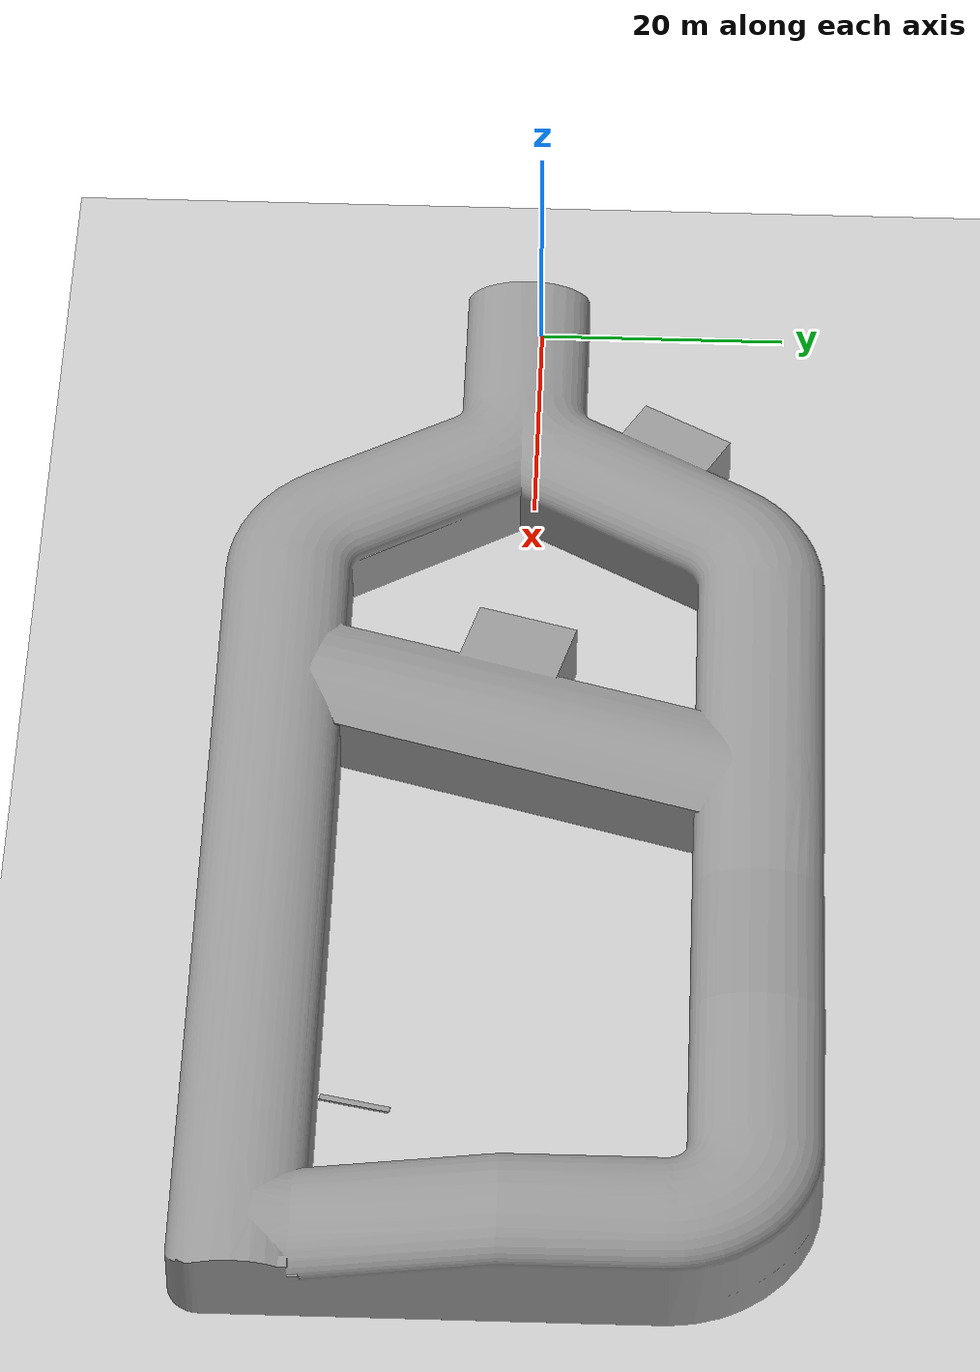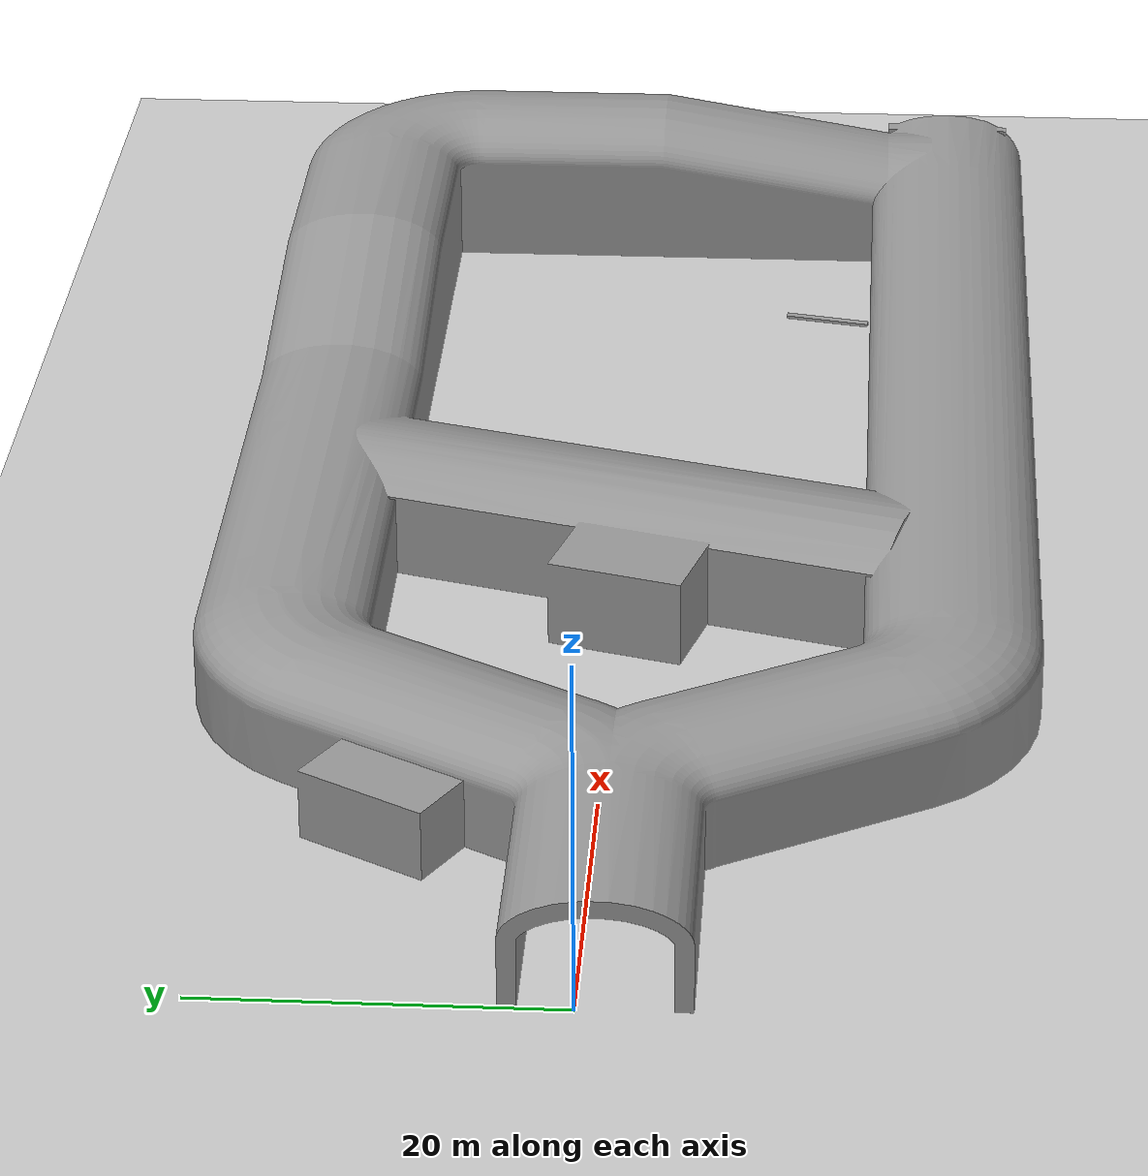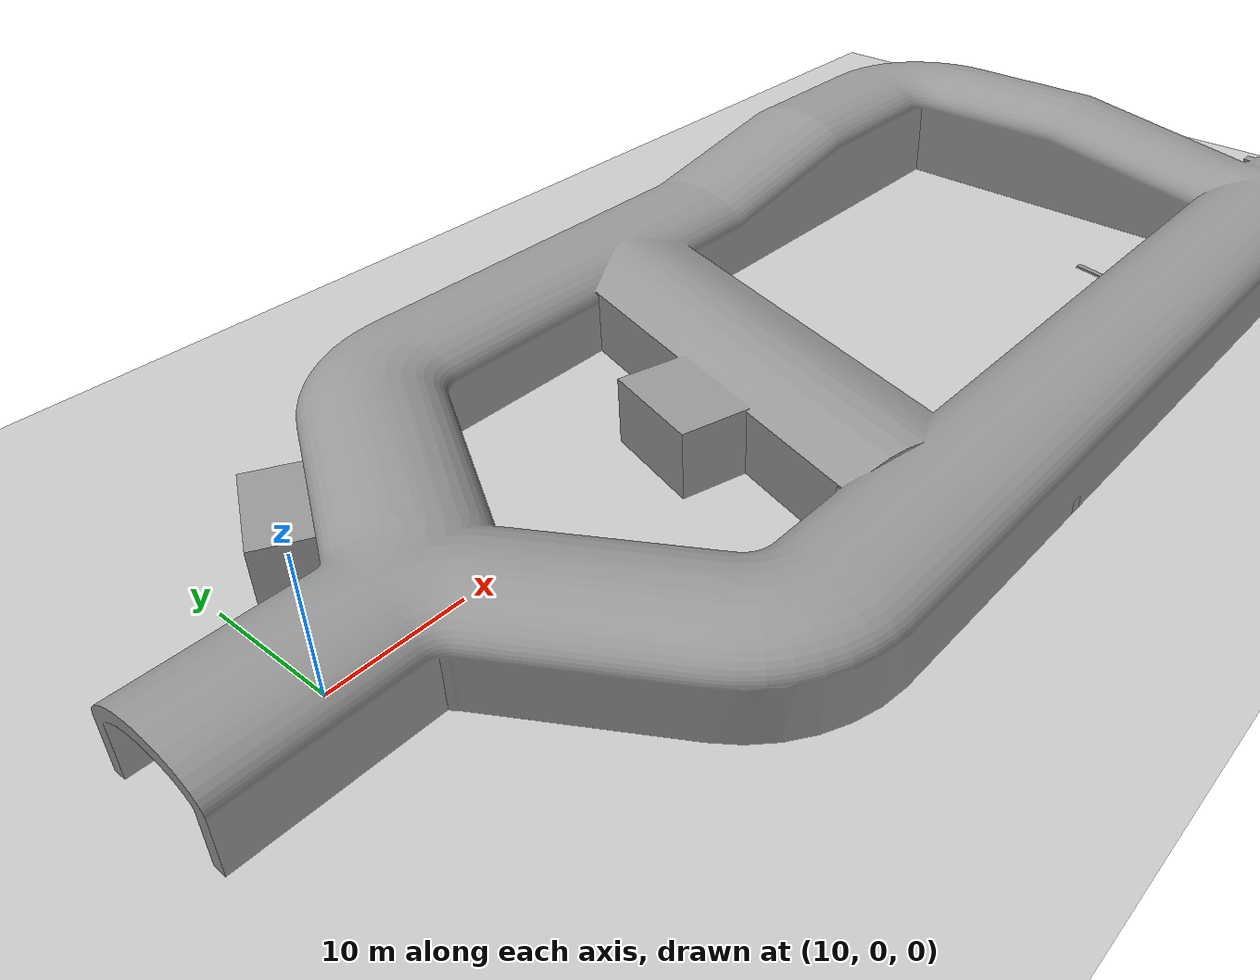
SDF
<sdf version="1.6">
 <world name="default">
  <light name="sun" type="directional">
   <pose>0 0 10 0 -0 0</pose>
   <diffuse>0.8 0.8 0.8 1</diffuse>
   <specular>0.2 0.2 0.2 1</specular>
   <attenuation>
    <range>1000</range>
    <constant>0.9</constant>
    <linear>0.01</linear>
    <quadratic>0.001</quadratic>
   </attenuation>
   <direction>-0.5 0.1 -0.9</direction>
  </light>
  <model name="ground_plane">
   <static>1</static>
   <link name="link">
    <collision name="collision">
     <geometry><plane><normal>0 0 1</normal><size>100 100</size></plane></geometry>
     <surface><friction><ode><mu>100</mu><mu2>50</mu2></ode></friction></surface>
    </collision>
    <visual name="visual">
     <cast_shadows>0</cast_shadows>
     <geometry><plane><normal>0 0 1</normal><size>100 100</size></plane></geometry>
    </visual>
   </link>
  </model>
  <gravity>0 0 -9.8</gravity>
  <magnetic_field>6e-06 2.3e-05 -4.2e-05</magnetic_field>
  <atmosphere type="adiabatic"/>
  <physics name="default_physics" default="0" type="ode">
   <max_step_size>0.001</max_step_size>
   <real_time_factor>1</real_time_factor>
   <real_time_update_rate>1000</real_time_update_rate>
  </physics>
  <scene><ambient>0.4 0.4 0.4 1</ambient><background>0.7 0.7 0.7 1</background><shadows>1</shadows></scene>
  <audio><device>default</device></audio>
  <spherical_coordinates>
   <surface_model>EARTH_WGS84</surface_model>
   <latitude_deg>0</latitude_deg>
   <longitude_deg>0</longitude_deg>
   <elevation>0</elevation>
   <heading_deg>0</heading_deg>
  </spherical_coordinates>
  <model name="hangdao">
   <link name="hangdao::link_0">
    <inertial>
     <mass>1e-08</mass>
     <inertia>
      <ixx>0.166667</ixx>
      <ixy>0</ixy>
      <ixz>0</ixz>
      <iyy>0.166667</iyy>
      <iyz>0</iyz>
      <izz>0.166667</izz>
     </inertia>
    </inertial>
    <pose>-2e-05 3e-06 0 0 -0 0</pose>
    <visual name="visual">
     <geometry>
      <mesh><uri>/home/xu/A_husky/src/husky/husky_gazebo/worlds/hangdao/hangdao.dae</uri><scale>1 1 1</scale></mesh>
     </geometry>
     <material>
      <lighting>1</lighting>
      <script><uri>file://media/materials/scripts/gazebo.material</uri><name>Gazebo/Grey</name></script>
     </material>
    </visual>
    <collision name="collision">
     <geometry>
      <mesh><uri>/home/xu/A_husky/src/husky/husky_gazebo/worlds/hangdao/hangdao.dae</uri><scale>1 1 1</scale></mesh>
     </geometry>
     <surface>
      <friction>
       <ode><mu>1</mu><mu2>1</mu2><fdir1>0 0 0</fdir1><slip1>0</slip1><slip2>0</slip2></ode>
       <torsional>
        <coefficient>1</coefficient>
        <patch_radius>0</patch_radius>
        <surface_radius>0</surface_radius>
        <use_patch_radius>1</use_patch_radius>
        <ode><slip>0</slip></ode>
       </torsional>
      </friction>
      <bounce><restitution_coefficient>0</restitution_coefficient><threshold>1e+06</threshold></bounce>
      <contact>
       <collide_without_contact>0</collide_without_contact>
       <collide_without_contact_bitmask>1</collide_without_contact_bitmask>
       <collide_bitmask>1</collide_bitmask>
       <ode>
        <soft_cfm>0</soft_cfm>
        <soft_erp>0.2</soft_erp>
        <kp>1e+13</kp>
        <kd>1</kd>
        <max_vel>0.01</max_vel>
        <min_depth>0</min_depth>
       </ode>
       <bullet>
        <split_impulse>1</split_impulse>
        <split_impulse_penetration_threshold>-0.01</split_impulse_penetration_threshold>
        <soft_cfm>0</soft_cfm>
        <soft_erp>0.2</soft_erp>
        <kp>1e+13</kp>
        <kd>1</kd>
       </bullet>
      </contact>
     </surface>
    </collision>
   </link>
   <static>1</static>
   <pose>0 24 0 0 0 -1.57</pose>
  </model>
  <light name="user_point_light_0" type="point">
   <pose>17.8312 -0.966396 1 0 -0 0</pose>
   <diffuse>0.5 0.5 0.5 1</diffuse>
   <specular>0.1 0.1 0.1 1</specular>
   <attenuation>
    <range>20</range>
    <constant>0.5</constant>
    <linear>0.01</linear>
    <quadratic>0.001</quadratic>
   </attenuation>
   <cast_shadows>0</cast_shadows>
   <direction>0 0 -1</direction>
  </light>
  <light name="user_point_light_1" type="point">
   <pose>6.00042 -0.731883 1 0 -0 0</pose>
   <diffuse>0.5 0.5 0.5 1</diffuse>
   <specular>0.1 0.1 0.1 1</specular>
   <attenuation>
    <range>20</range>
    <constant>0.5</constant>
    <linear>0.01</linear>
    <quadratic>0.001</quadratic>
   </attenuation>
   <cast_shadows>0</cast_shadows>
   <direction>0 0 -1</direction>
  </light>
  <light name="user_point_light_2" type="point">
   <pose>24.638 13.0518 1 0 -0 0</pose>
   <diffuse>0.5 0.5 0.5 1</diffuse>
   <specular>0.1 0.1 0.1 1</specular>
   <attenuation>
    <range>20</range>
    <constant>0.5</constant>
    <linear>0.01</linear>
    <quadratic>0.001</quadratic>
   </attenuation>
   <cast_shadows>0</cast_shadows>
   <direction>0 0 -1</direction>
  </light>
  <light name="user_point_light_3" type="point">
   <pose>26.0858 -16.8172 1 0 -0 0</pose>
   <diffuse>0.5 0.5 0.5 1</diffuse>
   <specular>0.1 0.1 0.1 1</specular>
   <attenuation>
    <range>20</range>
    <constant>0.5</constant>
    <linear>0.01</linear>
    <quadratic>0.001</quadratic>
   </attenuation>
   <cast_shadows>0</cast_shadows>
   <direction>0 0 -1</direction>
  </light>
  <light name="user_point_light_4" type="point">
   <pose>50.0139 18.1167 1 0 -0 0</pose>
   <diffuse>0.5 0.5 0.5 1</diffuse>
   <specular>0.1 0.1 0.1 1</specular>
   <attenuation>
    <range>20</range>
    <constant>0.5</constant>
    <linear>0.01</linear>
    <quadratic>0.001</quadratic>
   </attenuation>
   <cast_shadows>0</cast_shadows>
   <direction>0 0 -1</direction>
  </light>
  <light name="user_point_light_5" type="point">
   <pose>46.8086 -0.566852 1 0 -0 0</pose>
   <diffuse>0.5 0.5 0.5 1</diffuse>
   <specular>0.1 0.1 0.1 1</specular>
   <attenuation>
    <range>20</range>
    <constant>0.5</constant>
    <linear>0.01</linear>
    <quadratic>0.001</quadratic>
   </attenuation>
   <cast_shadows>0</cast_shadows>
   <direction>0 0 -1</direction>
  </light>
  <light name="user_point_light_6" type="point">
   <pose>41.9086 -18.8385 1 0 -0 0</pose>
   <diffuse>0.5 0.5 0.5 1</diffuse>
   <specular>0.1 0.1 0.1 1</specular>
   <attenuation>
    <range>20</range>
    <constant>0.5</constant>
    <linear>0.01</linear>
    <quadratic>0.001</quadratic>
   </attenuation>
   <cast_shadows>0</cast_shadows>
   <direction>0 0 -1</direction>
  </light>
  <light name="user_point_light_7" type="point">
   <pose>59.2735 -19.2199 1 0 -0 0</pose>
   <diffuse>0.5 0.5 0.5 1</diffuse>
   <specular>0.1 0.1 0.1 1</specular>
   <attenuation>
    <range>20</range>
    <constant>0.5</constant>
    <linear>0.01</linear>
    <quadratic>0.001</quadratic>
   </attenuation>
   <cast_shadows>0</cast_shadows>
   <direction>0 0 -1</direction>
  </light>
  <light name="user_point_light_8" type="point">
   <pose>75.0445 -19.2321 1 0 -0 0</pose>
   <diffuse>0.5 0.5 0.5 1</diffuse>
   <specular>0.1 0.1 0.1 1</specular>
   <attenuation>
    <range>20</range>
    <constant>0.5</constant>
    <linear>0.01</linear>
    <quadratic>0.001</quadratic>
   </attenuation>
   <cast_shadows>0</cast_shadows>
   <direction>0 0 -1</direction>
  </light>
  <light name="user_point_light_9" type="point">
   <pose>93.5256 -19.5946 1 0 -0 0</pose>
   <diffuse>0.5 0.5 0.5 1</diffuse>
   <specular>0.1 0.1 0.1 1</specular>
   <attenuation>
    <range>20</range>
    <constant>0.5</constant>
    <linear>0.01</linear>
    <quadratic>0.001</quadratic>
   </attenuation>
   <cast_shadows>0</cast_shadows>
   <direction>0 0 -1</direction>
  </light>
  <light name="user_point_light_10" type="point">
   <pose>67.0501 17.9549 1 0 -0 0</pose>
   <diffuse>0.5 0.5 0.5 1</diffuse>
   <specular>0.1 0.1 0.1 1</specular>
   <attenuation>
    <range>20</range>
    <constant>0.5</constant>
    <linear>0.01</linear>
    <quadratic>0.001</quadratic>
   </attenuation>
   <cast_shadows>0</cast_shadows>
   <direction>0 0 -1</direction>
  </light>
  <light name="user_point_light_11" type="point">
   <pose>88.6678 17.7042 1 0 -0 0</pose>
   <diffuse>0.5 0.5 0.5 1</diffuse>
   <specular>0.1 0.1 0.1 1</specular>
   <attenuation>
    <range>20</range>
    <constant>0.5</constant>
    <linear>0.01</linear>
    <quadratic>0.001</quadratic>
   </attenuation>
   <cast_shadows>0</cast_shadows>
   <direction>0 0 -1</direction>
  </light>
  <light name="user_point_light_12" type="point">
   <pose>96.2336 0.570116 1 0 -0 0</pose>
   <diffuse>0.5 0.5 0.5 1</diffuse>
   <specular>0.1 0.1 0.1 1</specular>
   <attenuation>
    <range>20</range>
    <constant>0.5</constant>
    <linear>0.01</linear>
    <quadratic>0.001</quadratic>
   </attenuation>
   <cast_shadows>0</cast_shadows>
   <direction>0 0 -1</direction>
  </light>
  <model name="unit_box">
   <pose>41.4714 -6.92045 0.5 0 0 -0.126627</pose>
   <link name="link">
    <inertial>
     <mass>1</mass>
     <inertia>
      <ixx>0.166667</ixx>
      <ixy>0</ixy>
      <ixz>0</ixz>
      <iyy>0.166667</iyy>
      <iyz>0</iyz>
      <izz>0.166667</izz>
     </inertia>
    </inertial>
    <collision name="collision"><geometry><box><size>1 1 1</size></box></geometry></collision>
    <visual name="visual">
     <geometry><box><size>1 1 1</size></box></geometry>
     <material>
      <script><name>Gazebo/Grey</name><uri>file://media/materials/scripts/gazebo.material</uri></script>
     </material>
    </visual>
   </link>
  </model>
  <model name="unit_box_0">
   <pose>41.0304 -3.57519 0.5 0 0 -0.077353</pose>
   <link name="link">
    <inertial>
     <mass>1</mass>
     <inertia>
      <ixx>0.166667</ixx>
      <ixy>0</ixy>
      <ixz>0</ixz>
      <iyy>0.166667</iyy>
      <iyz>0</iyz>
      <izz>0.166667</izz>
     </inertia>
    </inertial>
    <collision name="collision"><geometry><box><size>1 1 1</size></box></geometry></collision>
    <visual name="visual">
     <geometry><box><size>1 1 1</size></box></geometry>
     <material>
      <script><name>Gazebo/Grey</name><uri>file://media/materials/scripts/gazebo.material</uri></script>
     </material>
    </visual>
   </link>
  </model>
  <model name="unit_box_1">
   <pose>42.0446 -5.8583 0.5 0 -0 0.90067</pose>
   <link name="link">
    <inertial>
     <mass>1</mass>
     <inertia>
      <ixx>0.166667</ixx>
      <ixy>0</ixy>
      <ixz>0</ixz>
      <iyy>0.166667</iyy>
      <iyz>0</iyz>
      <izz>0.166667</izz>
     </inertia>
    </inertial>
    <collision name="collision"><geometry><box><size>1 1 1</size></box></geometry></collision>
    <visual name="visual">
     <geometry><box><size>1 1 1</size></box></geometry>
     <material>
      <script><name>Gazebo/Grey</name><uri>file://media/materials/scripts/gazebo.material</uri></script>
     </material>
    </visual>
   </link>
  </model>
  <model name="unit_box_2">
   <pose>51.8431 4.81712 0.5 0 -0 0.234699</pose>
   <link name="link">
    <inertial>
     <mass>1</mass>
     <inertia>
      <ixx>0.166667</ixx>
      <ixy>0</ixy>
      <ixz>0</ixz>
      <iyy>0.166667</iyy>
      <iyz>0</iyz>
      <izz>0.166667</izz>
     </inertia>
    </inertial>
    <collision name="collision"><geometry><box><size>1 1 1</size></box></geometry></collision>
    <visual name="visual">
     <geometry><box><size>1 1 1</size></box></geometry>
     <material>
      <script><name>Gazebo/Grey</name><uri>file://media/materials/scripts/gazebo.material</uri></script>
     </material>
    </visual>
   </link>
  </model>
  <model name="unit_box_3">
   <pose>51.5945 6.09987 0.5 0 -0 0.654509</pose>
   <link name="link">
    <inertial>
     <mass>1</mass>
     <inertia>
      <ixx>0.166667</ixx>
      <ixy>0</ixy>
      <ixz>0</ixz>
      <iyy>0.166667</iyy>
      <iyz>0</iyz>
      <izz>0.166667</izz>
     </inertia>
    </inertial>
    <collision name="collision"><geometry><box><size>1 1 1</size></box></geometry></collision>
    <visual name="visual">
     <geometry><box><size>1 1 1</size></box></geometry>
     <material>
      <script><name>Gazebo/Grey</name><uri>file://media/materials/scripts/gazebo.material</uri></script>
     </material>
    </visual>
   </link>
  </model>
  <model name="unit_box_4">
   <pose>50.6488 4.66727 0.499995 -5e-06 -1.57079 1.19484</pose>
   <link name="link">
    <inertial>
     <mass>1</mass>
     <inertia>
      <ixx>0.166667</ixx>
      <ixy>0</ixy>
      <ixz>0</ixz>
      <iyy>0.166667</iyy>
      <iyz>0</iyz>
      <izz>0.166667</izz>
     </inertia>
    </inertial>
    <collision name="collision"><geometry><box><size>1 1 1</size></box></geometry></collision>
    <visual name="visual">
     <geometry><box><size>1 1 1</size></box></geometry>
     <material>
      <script><name>Gazebo/Grey</name><uri>file://media/materials/scripts/gazebo.material</uri></script>
     </material>
    </visual>
   </link>
  </model>
  <model name="unit_box_5">
   <pose>57.7555 -16.0191 0.096425 0 -0 0.32523</pose>
   <link name="link">
    <inertial>
     <mass>1</mass>
     <inertia>
      <ixx>0.166667</ixx>
      <ixy>0</ixy>
      <ixz>0</ixz>
      <iyy>0.166667</iyy>
      <iyz>0</iyz>
      <izz>0.166667</izz>
     </inertia>
    </inertial>
    <collision name="collision"><geometry><box><size>1 0.452731 0.192851</size></box></geometry></collision>
    <visual name="visual">
     <geometry><box><size>1 0.452731 0.192851</size></box></geometry>
     <material>
      <script><name>Gazebo/Grey</name><uri>file://media/materials/scripts/gazebo.material</uri></script>
     </material>
    </visual>
   </link>
  </model>
  <model name="unit_box_6">
   <pose>54.955 -15.8352 0.499995 0 1e-05 -2e-06</pose>
   <link name="link">
    <inertial>
     <mass>1</mass>
     <inertia>
      <ixx>0.166667</ixx>
      <ixy>0</ixy>
      <ixz>0</ixz>
      <iyy>0.166667</iyy>
      <iyz>0</iyz>
      <izz>0.166667</izz>
     </inertia>
    </inertial>
    <collision name="collision"><geometry><box><size>1 1 1</size></box></geometry></collision>
    <visual name="visual">
     <geometry><box><size>1 1 1</size></box></geometry>
     <material>
      <script><name>Gazebo/Grey</name><uri>file://media/materials/scripts/gazebo.material</uri></script>
     </material>
    </visual>
   </link>
  </model>
  <model name="unit_box_7">
   <pose>56.317 -16.6763 0.499999 0 0 -0.001364</pose>
   <link name="link">
    <inertial>
     <mass>1</mass>
     <inertia>
      <ixx>0.166667</ixx>
      <ixy>0</ixy>
      <ixz>0</ixz>
      <iyy>0.166667</iyy>
      <iyz>0</iyz>
      <izz>0.166667</izz>
     </inertia>
    </inertial>
    <collision name="collision"><geometry><box><size>1 0.999999 0.999999</size></box></geometry></collision>
    <visual name="visual">
     <geometry><box><size>1 0.999999 0.999999</size></box></geometry>
     <material>
      <script><name>Gazebo/Grey</name><uri>file://media/materials/scripts/gazebo.material</uri></script>
     </material>
    </visual>
   </link>
  </model>
  <model name="unit_box_8_clone">
   <pose>21.629 -5.33666 0.118862 6e-06 -0.000971 -1.61786</pose>
   <link name="link">
    <inertial>
     <mass>1</mass>
     <inertia>
      <ixx>0.166667</ixx>
      <ixy>0</ixy>
      <ixz>0</ixz>
      <iyy>0.166667</iyy>
      <iyz>0</iyz>
      <izz>0.166667</izz>
     </inertia>
    </inertial>
    <collision name="collision"><geometry><box><size>4.79587 0.517599 0.242375</size></box></geometry></collision>
    <visual name="visual">
     <geometry><box><size>4.79587 0.517599 0.242375</size></box></geometry>
     <material>
      <script><name>Gazebo/Grey</name><uri>file://media/materials/scripts/gazebo.material</uri></script>
     </material>
    </visual>
   </link>
  </model>
  <model name="unit_box_9">
   <pose>24.1258 -7.5853 0.499996 0 -9e-06 0.13837</pose>
   <link name="link">
    <inertial>
     <mass>1</mass>
     <inertia>
      <ixx>0.166667</ixx>
      <ixy>0</ixy>
      <ixz>0</ixz>
      <iyy>0.166667</iyy>
      <iyz>0</iyz>
      <izz>0.166667</izz>
     </inertia>
    </inertial>
    <collision name="collision"><geometry><box><size>1 1 1</size></box></geometry></collision>
    <visual name="visual">
     <geometry><box><size>1 1 1</size></box></geometry>
     <material>
      <script><name>Gazebo/Grey</name><uri>file://media/materials/scripts/gazebo.material</uri></script>
     </material>
    </visual>
   </link>
  </model>
  <model name="unit_box_10">
   <pose>22.5215 -6.7081 0.499995 -1.57079 -1.57079 1.48797</pose>
   <link name="link">
    <inertial>
     <mass>1</mass>
     <inertia>
      <ixx>0.166667</ixx>
      <ixy>0</ixy>
      <ixz>0</ixz>
      <iyy>0.166667</iyy>
      <iyz>0</iyz>
      <izz>0.166667</izz>
     </inertia>
    </inertial>
    <collision name="collision"><geometry><box><size>1 1 1</size></box></geometry></collision>
    <visual name="visual">
     <geometry><box><size>1 1 1</size></box></geometry>
     <material>
      <script><name>Gazebo/Grey</name><uri>file://media/materials/scripts/gazebo.material</uri></script>
     </material>
    </visual>
   </link>
  </model>
  <model name="unit_sphere">
   <pose>22.3734 -4.09521 0.5 -0.268434 0.182582 2.81227</pose>
   <link name="link">
    <inertial>
     <mass>1</mass>
     <inertia><ixx>0.1</ixx><ixy>0</ixy><ixz>0</ixz><iyy>0.1</iyy><iyz>0</iyz><izz>0.1</izz></inertia>
    </inertial>
    <collision name="collision"><geometry><sphere><radius>0.5</radius></sphere></geometry></collision>
    <visual name="visual">
     <geometry><sphere><radius>0.5</radius></sphere></geometry>
     <material>
      <script><name>Gazebo/Grey</name><uri>file://media/materials/scripts/gazebo.material</uri></script>
     </material>
    </visual>
   </link>
  </model>
  <model name="unit_box_12">
   <pose>19.2037 -11.7334 0.5 0 -0 1.03868</pose>
   <link name="link">
    <inertial>
     <mass>1</mass>
     <inertia>
      <ixx>0.166667</ixx>
      <ixy>0</ixy>
      <ixz>0</ixz>
      <iyy>0.166667</iyy>
      <iyz>0</iyz>
      <izz>0.166667</izz>
     </inertia>
    </inertial>
    <collision name="collision"><geometry><box><size>1 1 1</size></box></geometry></collision>
    <visual name="visual">
     <geometry><box><size>1 1 1</size></box></geometry>
     <material>
      <script><name>Gazebo/Grey</name><uri>file://media/materials/scripts/gazebo.material</uri></script>
     </material>
    </visual>
   </link>
  </model>
  <model name="unit_sphere_0">
   <pose>18.3546 -11.2029 0.5 -1.68202 -0.18753 0.304167</pose>
   <link name="link">
    <inertial>
     <mass>1</mass>
     <inertia><ixx>0.1</ixx><ixy>0</ixy><ixz>0</ixz><iyy>0.1</iyy><iyz>0</iyz><izz>0.1</izz></inertia>
    </inertial>
    <collision name="collision"><geometry><sphere><radius>0.5</radius></sphere></geometry></collision>
    <visual name="visual">
     <geometry><sphere><radius>0.5</radius></sphere></geometry>
     <material>
      <script><name>Gazebo/Grey</name><uri>file://media/materials/scripts/gazebo.material</uri></script>
     </material>
    </visual>
   </link>
  </model>
  <model name="unit_box_8_clone_0">
   <pose>25.892 18.8833 0.499999 0 0 -0.835221</pose>
   <link name="link">
    <inertial>
     <mass>1</mass>
     <inertia>
      <ixx>0.166667</ixx>
      <ixy>0</ixy>
      <ixz>0</ixz>
      <iyy>0.166667</iyy>
      <iyz>0</iyz>
      <izz>0.166667</izz>
     </inertia>
    </inertial>
    <collision name="collision"><geometry><box><size>1 0.999998 0.999998</size></box></geometry></collision>
    <visual name="visual">
     <geometry><box><size>1 0.999998 0.999998</size></box></geometry>
     <material>
      <script><name>Gazebo/Grey</name><uri>file://media/materials/scripts/gazebo.material</uri></script>
     </material>
    </visual>
   </link>
  </model>
  <model name="unit_box_8_clone_clone_clone">
   <pose>22.6599 15.2628 0.121185 1e-06 2e-06 -2.50597</pose>
   <link name="link">
    <inertial>
     <mass>1</mass>
     <inertia>
      <ixx>0.166667</ixx>
      <ixy>0</ixy>
      <ixz>0</ixz>
      <iyy>0.166667</iyy>
      <iyz>0</iyz>
      <izz>0.166667</izz>
     </inertia>
    </inertial>
    <collision name="collision"><geometry><box><size>4.79587 0.517599 0.242377</size></box></geometry></collision>
    <visual name="visual">
     <geometry><box><size>4.79587 0.517599 0.242377</size></box></geometry>
     <material>
      <script><name>Gazebo/Grey</name><uri>file://media/materials/scripts/gazebo.material</uri></script>
     </material>
    </visual>
   </link>
  </model>
  <model name="unit_sphere_1">
   <pose>24.5927 18.2957 0.5 1.7e-05 -0.000279 -0.000211</pose>
   <link name="link">
    <inertial>
     <mass>1</mass>
     <inertia><ixx>0.1</ixx><ixy>0</ixy><ixz>0</ixz><iyy>0.1</iyy><iyz>0</iyz><izz>0.1</izz></inertia>
    </inertial>
    <collision name="collision"><geometry><sphere><radius>0.5</radius></sphere></geometry></collision>
    <visual name="visual">
     <geometry><sphere><radius>0.5</radius></sphere></geometry>
     <material>
      <script><name>Gazebo/Grey</name><uri>file://media/materials/scripts/gazebo.material</uri></script>
     </material>
    </visual>
   </link>
  </model>
  <model name="unit_box_13">
   <pose>28.1368 20.5856 0.499995 0 1e-05 -5e-06</pose>
   <link name="link">
    <inertial>
     <mass>1</mass>
     <inertia>
      <ixx>0.166667</ixx>
      <ixy>0</ixy>
      <ixz>0</ixz>
      <iyy>0.166667</iyy>
      <iyz>0</iyz>
      <izz>0.166667</izz>
     </inertia>
    </inertial>
    <collision name="collision"><geometry><box><size>1 1 1</size></box></geometry></collision>
    <visual name="visual">
     <geometry><box><size>1 1 1</size></box></geometry>
     <material>
      <script><name>Gazebo/Grey</name><uri>file://media/materials/scripts/gazebo.material</uri></script>
     </material>
    </visual>
   </link>
  </model>
  <model name="unit_box_14">
   <pose>30.2002 21.0256 0.5 0 -0 0.452301</pose>
   <link name="link">
    <inertial>
     <mass>1</mass>
     <inertia>
      <ixx>0.166667</ixx>
      <ixy>0</ixy>
      <ixz>0</ixz>
      <iyy>0.166667</iyy>
      <iyz>0</iyz>
      <izz>0.166667</izz>
     </inertia>
    </inertial>
    <collision name="collision"><geometry><box><size>1 1 1</size></box></geometry></collision>
    <visual name="visual">
     <geometry><box><size>1 1 1</size></box></geometry>
     <material>
      <script><name>Gazebo/Grey</name><uri>file://media/materials/scripts/gazebo.material</uri></script>
     </material>
    </visual>
   </link>
  </model>
  <model name="unit_box_16">
   <pose>69.939 -22.2819 0.499995 0 1e-05 0.022827</pose>
   <link name="link">
    <inertial>
     <mass>1</mass>
     <inertia>
      <ixx>0.166667</ixx>
      <ixy>0</ixy>
      <ixz>0</ixz>
      <iyy>0.166667</iyy>
      <iyz>0</iyz>
      <izz>0.166667</izz>
     </inertia>
    </inertial>
    <collision name="collision"><geometry><box><size>1 1 1</size></box></geometry></collision>
    <visual name="visual">
     <geometry><box><size>1 1 1</size></box></geometry>
     <material>
      <script><name>Gazebo/Grey</name><uri>file://media/materials/scripts/gazebo.material</uri></script>
     </material>
    </visual>
   </link>
  </model>
  <model name="unit_box_17">
   <pose>80.211 -16.617 0.499998 0 -0 0.859609</pose>
   <link name="link">
    <inertial>
     <mass>1</mass>
     <inertia>
      <ixx>0.166667</ixx>
      <ixy>0</ixy>
      <ixz>0</ixz>
      <iyy>0.166667</iyy>
      <iyz>0</iyz>
      <izz>0.166667</izz>
     </inertia>
    </inertial>
    <collision name="collision">
     <geometry><box><size>0.999997 0.999998 0.999996</size></box></geometry>
    </collision>
    <visual name="visual">
     <geometry><box><size>0.999997 0.999998 0.999996</size></box></geometry>
     <material>
      <script><name>Gazebo/Grey</name><uri>file://media/materials/scripts/gazebo.material</uri></script>
     </material>
    </visual>
   </link>
  </model>
  <model name="unit_box_18">
   <pose>31.0033 -20.1925 0.499995 0 1e-05 0.122617</pose>
   <link name="link">
    <inertial>
     <mass>1</mass>
     <inertia>
      <ixx>0.166667</ixx>
      <ixy>0</ixy>
      <ixz>0</ixz>
      <iyy>0.166667</iyy>
      <iyz>0</iyz>
      <izz>0.166667</izz>
     </inertia>
    </inertial>
    <collision name="collision"><geometry><box><size>1 1 1</size></box></geometry></collision>
    <visual name="visual">
     <geometry><box><size>1 1 1</size></box></geometry>
     <material>
      <script><name>Gazebo/Grey</name><uri>file://media/materials/scripts/gazebo.material</uri></script>
     </material>
    </visual>
   </link>
  </model>
  <model name="unit_box_19">
   <pose>29.355 -21.5353 0.499995 1e-05 -0 -0.000251</pose>
   <link name="link">
    <inertial>
     <mass>1</mass>
     <inertia>
      <ixx>0.166667</ixx>
      <ixy>0</ixy>
      <ixz>0</ixz>
      <iyy>0.166667</iyy>
      <iyz>0</iyz>
      <izz>0.166667</izz>
     </inertia>
    </inertial>
    <collision name="collision"><geometry><box><size>1 1 1</size></box></geometry></collision>
    <visual name="visual">
     <geometry><box><size>1 1 1</size></box></geometry>
     <material>
      <script><name>Gazebo/Grey</name><uri>file://media/materials/scripts/gazebo.material</uri></script>
     </material>
    </visual>
   </link>
  </model>
  <model name="unit_box_8_clone_1">
   <pose>33.0467 -21.6306 0.499998 0 0 -0.835213</pose>
   <link name="link">
    <inertial>
     <mass>1</mass>
     <inertia>
      <ixx>0.166667</ixx>
      <ixy>0</ixy>
      <ixz>0</ixz>
      <iyy>0.166667</iyy>
      <iyz>0</iyz>
      <izz>0.166667</izz>
     </inertia>
    </inertial>
    <collision name="collision"><geometry><box><size>1 0.999998 0.999997</size></box></geometry></collision>
    <visual name="visual">
     <geometry><box><size>1 0.999998 0.999997</size></box></geometry>
     <material>
      <script><name>Gazebo/Grey</name><uri>file://media/materials/scripts/gazebo.material</uri></script>
     </material>
    </visual>
   </link>
  </model>
  <model name="unit_box_20">
   <pose>30.0029 -20.4988 0.499995 -1.57081 -0 1.63074</pose>
   <link name="link">
    <inertial>
     <mass>1</mass>
     <inertia>
      <ixx>0.166667</ixx>
      <ixy>0</ixy>
      <ixz>0</ixz>
      <iyy>0.166667</iyy>
      <iyz>0</iyz>
      <izz>0.166667</izz>
     </inertia>
    </inertial>
    <collision name="collision"><geometry><box><size>1 1 1</size></box></geometry></collision>
    <visual name="visual">
     <geometry><box><size>1 1 1</size></box></geometry>
     <material>
      <script><name>Gazebo/Grey</name><uri>file://media/materials/scripts/gazebo.material</uri></script>
     </material>
    </visual>
   </link>
  </model>
  <model name="unit_box_21">
   <pose>89.1775 -22.4495 0.5 0 -0 0.2806</pose>
   <link name="link">
    <inertial>
     <mass>1</mass>
     <inertia>
      <ixx>0.166667</ixx>
      <ixy>0</ixy>
      <ixz>0</ixz>
      <iyy>0.166667</iyy>
      <iyz>0</iyz>
      <izz>0.166667</izz>
     </inertia>
    </inertial>
    <collision name="collision"><geometry><box><size>1 1 1</size></box></geometry></collision>
    <visual name="visual">
     <geometry><box><size>1 1 1</size></box></geometry>
     <material>
      <script><name>Gazebo/Grey</name><uri>file://media/materials/scripts/gazebo.material</uri></script>
     </material>
    </visual>
   </link>
  </model>
  <model name="unit_box_22">
   <pose>83.356 -16.0066 0.499998 0 -0 -0.587225</pose>
   <link name="link">
    <inertial>
     <mass>1</mass>
     <inertia>
      <ixx>0.166667</ixx>
      <ixy>0</ixy>
      <ixz>0</ixz>
      <iyy>0.166667</iyy>
      <iyz>0</iyz>
      <izz>0.166667</izz>
     </inertia>
    </inertial>
    <collision name="collision"><geometry><box><size>0.999997 1 0.999997</size></box></geometry></collision>
    <visual name="visual">
     <geometry><box><size>0.999997 1 0.999997</size></box></geometry>
     <material>
      <script><name>Gazebo/Grey</name><uri>file://media/materials/scripts/gazebo.material</uri></script>
     </material>
    </visual>
   </link>
  </model>
  <light name="user_point_light_13" type="point">
   <pose>19.8151 23.9411 1 0 -0 0</pose>
   <diffuse>0.5 0.5 0.5 1</diffuse>
   <specular>0.1 0.1 0.1 1</specular>
   <attenuation>
    <range>20</range>
    <constant>0.5</constant>
    <linear>0.01</linear>
    <quadratic>0.001</quadratic>
   </attenuation>
   <cast_shadows>0</cast_shadows>
   <direction>0 0 -1</direction>
  </light>
  <light name="user_point_light_14" type="point">
   <pose>17.1871 24.4869 1 0 -0 0</pose>
   <diffuse>0.5 0.5 0.5 1</diffuse>
   <specular>0.1 0.1 0.1 1</specular>
   <attenuation>
    <range>20</range>
    <constant>0.5</constant>
    <linear>0.01</linear>
    <quadratic>0.001</quadratic>
   </attenuation>
   <cast_shadows>0</cast_shadows>
   <direction>0 0 -1</direction>
  </light>
  <model name="unit_box_23">
   <pose>44.961 -22.2562 0.5 0 -0 0.449288</pose>
   <link name="link">
    <inertial>
     <mass>1</mass>
     <inertia>
      <ixx>0.166667</ixx>
      <ixy>0</ixy>
      <ixz>0</ixz>
      <iyy>0.166667</iyy>
      <iyz>0</iyz>
      <izz>0.166667</izz>
     </inertia>
    </inertial>
    <collision name="collision"><geometry><box><size>1 1 1</size></box></geometry></collision>
    <visual name="visual">
     <geometry><box><size>1 1 1</size></box></geometry>
     <material>
      <script><name>Gazebo/Grey</name><uri>file://media/materials/scripts/gazebo.material</uri></script>
     </material>
    </visual>
   </link>
  </model>
  <model name="unit_box_24">
   <pose>50.7297 -23.6615 0.500006 1e-06 5e-06 0.0008</pose>
   <link name="link">
    <inertial>
     <mass>1</mass>
     <inertia>
      <ixx>0.166667</ixx>
      <ixy>0</ixy>
      <ixz>0</ixz>
      <iyy>0.166667</iyy>
      <iyz>0</iyz>
      <izz>0.166667</izz>
     </inertia>
    </inertial>
    <collision name="collision"><geometry><box><size>1 1 1</size></box></geometry></collision>
    <visual name="visual">
     <geometry><box><size>1 1 1</size></box></geometry>
     <material>
      <script><name>Gazebo/Grey</name><uri>file://media/materials/scripts/gazebo.material</uri></script>
     </material>
    </visual>
   </link>
  </model>
  <model name="unit_box_25">
   <pose>93.3866 5.97098 3.00001 0 -0 -0.379821</pose>
   <link name="link">
    <inertial>
     <mass>1</mass>
     <inertia>
      <ixx>0.166667</ixx>
      <ixy>0</ixy>
      <ixz>0</ixz>
      <iyy>0.166667</iyy>
      <iyz>0</iyz>
      <izz>0.166667</izz>
     </inertia>
    </inertial>
    <collision name="collision"><geometry><box><size>1 1 1</size></box></geometry></collision>
    <visual name="visual">
     <geometry><box><size>1 1 1</size></box></geometry>
     <material>
      <script><name>Gazebo/Grey</name><uri>file://media/materials/scripts/gazebo.material</uri></script>
     </material>
    </visual>
   </link>
  </model>
  <light name="user_point_light_15" type="point">
   <pose>80.9531 -73.5946 1 0 -0 0</pose>
   <diffuse>0.5 0.5 0.5 1</diffuse>
   <specular>0.1 0.1 0.1 1</specular>
   <attenuation>
    <range>20</range>
    <constant>0.5</constant>
    <linear>0.01</linear>
    <quadratic>0.001</quadratic>
   </attenuation>
   <cast_shadows>0</cast_shadows>
   <direction>0 0 -1</direction>
  </light>
  <model name="unit_box_26">
   <pose>98.812 -6.35157 1.96885 0.165149 0.000132 7e-06</pose>
   <link name="link">
    <inertial>
     <mass>1</mass>
     <inertia>
      <ixx>0.166667</ixx>
      <ixy>0</ixy>
      <ixz>0</ixz>
      <iyy>0.166667</iyy>
      <iyz>0</iyz>
      <izz>0.166667</izz>
     </inertia>
    </inertial>
    <collision name="collision"><geometry><box><size>1 1 1</size></box></geometry></collision>
    <visual name="visual">
     <geometry><box><size>1 1 1</size></box></geometry>
     <material>
      <script><name>Gazebo/Grey</name><uri>file://media/materials/scripts/gazebo.material</uri></script>
     </material>
    </visual>
   </link>
  </model>
  <model name="unit_box_26_clone">
   <pose>93.15 -10.4727 1.28275 0.165149 0.000126 3.8e-05</pose>
   <link name="link">
    <inertial>
     <mass>1</mass>
     <inertia>
      <ixx>0.166667</ixx>
      <ixy>0</ixy>
      <ixz>0</ixz>
      <iyy>0.166667</iyy>
      <iyz>0</iyz>
      <izz>0.166667</izz>
     </inertia>
    </inertial>
    <collision name="collision"><geometry><box><size>1 1 1</size></box></geometry></collision>
    <visual name="visual">
     <geometry><box><size>1 1 1</size></box></geometry>
     <material>
      <script><name>Gazebo/Grey</name><uri>file://media/materials/scripts/gazebo.material</uri></script>
     </material>
    </visual>
   </link>
  </model>
  <model name="unit_box_26_clone_0">
   <pose>99.5662 -14.0398 0.687377 0.165152 0.000398 -0.001591</pose>
   <link name="link">
    <inertial>
     <mass>1</mass>
     <inertia>
      <ixx>0.166667</ixx>
      <ixy>0</ixy>
      <ixz>0</ixz>
      <iyy>0.166667</iyy>
      <iyz>0</iyz>
      <izz>0.166667</izz>
     </inertia>
    </inertial>
    <collision name="collision"><geometry><box><size>1 1 1</size></box></geometry></collision>
    <visual name="visual">
     <geometry><box><size>1 1 1</size></box></geometry>
     <material>
      <script><name>Gazebo/Grey</name><uri>file://media/materials/scripts/gazebo.material</uri></script>
     </material>
    </visual>
   </link>
  </model>
  <model name="unit_box_26_clone_0_clone">
   <pose>98.675 -3.58129 2.43058 0.165139 -0.001801 0.011605</pose>
   <link name="link">
    <inertial>
     <mass>1</mass>
     <inertia>
      <ixx>0.166667</ixx>
      <ixy>0</ixy>
      <ixz>0</ixz>
      <iyy>0.166667</iyy>
      <iyz>0</iyz>
      <izz>0.166667</izz>
     </inertia>
    </inertial>
    <collision name="collision"><geometry><box><size>1 1 1</size></box></geometry></collision>
    <visual name="visual">
     <geometry><box><size>1 1 1</size></box></geometry>
     <material>
      <script><name>Gazebo/Grey</name><uri>file://media/materials/scripts/gazebo.material</uri></script>
     </material>
    </visual>
   </link>
  </model>
  <model name="unit_box_26_clone_0_clone_0">
   <pose>93.331 -8.27111 1.64965 0.165148 0.000447 -0.001884</pose>
   <link name="link">
    <inertial>
     <mass>1</mass>
     <inertia>
      <ixx>0.166667</ixx>
      <ixy>0</ixy>
      <ixz>0</ixz>
      <iyy>0.166667</iyy>
      <iyz>0</iyz>
      <izz>0.166667</izz>
     </inertia>
    </inertial>
    <collision name="collision"><geometry><box><size>1 1 1</size></box></geometry></collision>
    <visual name="visual">
     <geometry><box><size>1 1 1</size></box></geometry>
     <material>
      <script><name>Gazebo/Grey</name><uri>file://media/materials/scripts/gazebo.material</uri></script>
     </material>
    </visual>
   </link>
  </model>
  <model name="unit_box_26_clone_0_clone_1">
   <pose>98.6506 -9.66818 1.4161 0.165148 0.000448 -0.001894</pose>
   <link name="link">
    <inertial>
     <mass>1</mass>
     <inertia>
      <ixx>0.166667</ixx>
      <ixy>0</ixy>
      <ixz>0</ixz>
      <iyy>0.166667</iyy>
      <iyz>0</iyz>
      <izz>0.166667</izz>
     </inertia>
    </inertial>
    <collision name="collision"><geometry><box><size>1 1 1</size></box></geometry></collision>
    <visual name="visual">
     <geometry><box><size>1 1 1</size></box></geometry>
     <material>
      <script><name>Gazebo/Grey</name><uri>file://media/materials/scripts/gazebo.material</uri></script>
     </material>
    </visual>
   </link>
  </model>
  <model name="unit_box_25_clone">
   <pose>98.8348 2.05797 3.00001 0 -0 0.592525</pose>
   <link name="link">
    <inertial>
     <mass>1</mass>
     <inertia>
      <ixx>0.166667</ixx>
      <ixy>0</ixy>
      <ixz>0</ixz>
      <iyy>0.166667</iyy>
      <iyz>0</iyz>
      <izz>0.166667</izz>
     </inertia>
    </inertial>
    <collision name="collision"><geometry><box><size>1 1 1</size></box></geometry></collision>
    <visual name="visual">
     <geometry><box><size>1 1 1</size></box></geometry>
     <material>
      <script><name>Gazebo/Grey</name><uri>file://media/materials/scripts/gazebo.material</uri></script>
     </material>
    </visual>
   </link>
  </model>
  <model name="unit_box_25_clone_0">
   <pose>98.4857 11.9865 3.00001 0 -0 0.366055</pose>
   <link name="link">
    <inertial>
     <mass>1</mass>
     <inertia>
      <ixx>0.166667</ixx>
      <ixy>0</ixy>
      <ixz>0</ixz>
      <iyy>0.166667</iyy>
      <iyz>0</iyz>
      <izz>0.166667</izz>
     </inertia>
    </inertial>
    <collision name="collision"><geometry><box><size>1 1 1</size></box></geometry></collision>
    <visual name="visual">
     <geometry><box><size>1 1 1</size></box></geometry>
     <material>
      <script><name>Gazebo/Grey</name><uri>file://media/materials/scripts/gazebo.material</uri></script>
     </material>
    </visual>
   </link>
  </model>
  <model name="unit_box_27">
   <pose>42.6981 15.1111 0.499995 -0 -1e-05 -2e-05</pose>
   <link name="link">
    <inertial>
     <mass>1</mass>
     <inertia>
      <ixx>0.166667</ixx>
      <ixy>0</ixy>
      <ixz>0</ixz>
      <iyy>0.166667</iyy>
      <iyz>0</iyz>
      <izz>0.166667</izz>
     </inertia>
    </inertial>
    <collision name="collision"><geometry><box><size>1 1 1</size></box></geometry></collision>
    <visual name="visual">
     <geometry><box><size>1 1 1</size></box></geometry>
     <material>
      <script><name>Gazebo/Grey</name><uri>file://media/materials/scripts/gazebo.material</uri></script>
     </material>
    </visual>
   </link>
  </model>
  <model name="unit_box_28">
   <pose>44.522 21.7416 0.499995 -0 1e-05 -2.6e-05</pose>
   <link name="link">
    <inertial>
     <mass>1</mass>
     <inertia>
      <ixx>0.166667</ixx>
      <ixy>0</ixy>
      <ixz>0</ixz>
      <iyy>0.166667</iyy>
      <iyz>0</iyz>
      <izz>0.166667</izz>
     </inertia>
    </inertial>
    <collision name="collision"><geometry><box><size>1 1 1</size></box></geometry></collision>
    <visual name="visual">
     <geometry><box><size>1 1 1</size></box></geometry>
     <material>
      <script><name>Gazebo/Grey</name><uri>file://media/materials/scripts/gazebo.material</uri></script>
     </material>
    </visual>
   </link>
  </model>
  <model name="unit_box_29">
   <pose>39.8352 15.0976 0.499995 0 1e-05 -5e-06</pose>
   <link name="link">
    <inertial>
     <mass>1</mass>
     <inertia>
      <ixx>0.166667</ixx>
      <ixy>0</ixy>
      <ixz>0</ixz>
      <iyy>0.166667</iyy>
      <iyz>0</iyz>
      <izz>0.166667</izz>
     </inertia>
    </inertial>
    <collision name="collision"><geometry><box><size>1 1 1</size></box></geometry></collision>
    <visual name="visual">
     <geometry><box><size>1 1 1</size></box></geometry>
     <material>
      <script><name>Gazebo/Grey</name><uri>file://media/materials/scripts/gazebo.material</uri></script>
     </material>
    </visual>
   </link>
  </model>
  <model name="unit_box_30">
   <pose>38.3279 21.3728 0.494445 0.000851 0.005459 0.161318</pose>
   <link name="link">
    <inertial>
     <mass>1</mass>
     <inertia>
      <ixx>0.166667</ixx>
      <ixy>0</ixy>
      <ixz>0</ixz>
      <iyy>0.166667</iyy>
      <iyz>0</iyz>
      <izz>0.166667</izz>
     </inertia>
    </inertial>
    <collision name="collision"><geometry><box><size>1 1 1</size></box></geometry></collision>
    <visual name="visual">
     <geometry><box><size>1 1 1</size></box></geometry>
     <material>
      <script><name>Gazebo/Grey</name><uri>file://media/materials/scripts/gazebo.material</uri></script>
     </material>
    </visual>
   </link>
  </model>
  <model name="unit_box_31">
   <pose>59.0723 21.3567 0.499995 1e-05 -0 -1.1e-05</pose>
   <link name="link">
    <inertial>
     <mass>1</mass>
     <inertia>
      <ixx>0.166667</ixx>
      <ixy>0</ixy>
      <ixz>0</ixz>
      <iyy>0.166667</iyy>
      <iyz>0</iyz>
      <izz>0.166667</izz>
     </inertia>
    </inertial>
    <collision name="collision"><geometry><box><size>1 1 1</size></box></geometry></collision>
    <visual name="visual">
     <geometry><box><size>1 1 1</size></box></geometry>
     <material>
      <script><name>Gazebo/Grey</name><uri>file://media/materials/scripts/gazebo.material</uri></script>
     </material>
    </visual>
   </link>
  </model>
  <model name="unit_box_31_clone">
   <pose>75.3655 15.7298 2.71065 0.000165 -0.175238 -0.000152</pose>
   <link name="link">
    <inertial>
     <mass>1</mass>
     <inertia>
      <ixx>0.166667</ixx>
      <ixy>0</ixy>
      <ixz>0</ixz>
      <iyy>0.166667</iyy>
      <iyz>0</iyz>
      <izz>0.166667</izz>
     </inertia>
    </inertial>
    <collision name="collision"><geometry><box><size>1 1 1</size></box></geometry></collision>
    <visual name="visual">
     <geometry><box><size>1 1 1</size></box></geometry>
     <material>
      <script><name>Gazebo/Grey</name><uri>file://media/materials/scripts/gazebo.material</uri></script>
     </material>
    </visual>
   </link>
  </model>
  <model name="unit_box_31_clone_0">
   <pose>68.3762 20.871 1.47389 0.000313 -0.175237 -0.000998</pose>
   <link name="link">
    <inertial>
     <mass>1</mass>
     <inertia>
      <ixx>0.166667</ixx>
      <ixy>0</ixy>
      <ixz>0</ixz>
      <iyy>0.166667</iyy>
      <iyz>0</iyz>
      <izz>0.166667</izz>
     </inertia>
    </inertial>
    <collision name="collision"><geometry><box><size>1 1 1</size></box></geometry></collision>
    <visual name="visual">
     <geometry><box><size>1 1 1</size></box></geometry>
     <material>
      <script><name>Gazebo/Grey</name><uri>file://media/materials/scripts/gazebo.material</uri></script>
     </material>
    </visual>
   </link>
  </model>
  <model name="unit_box_31_clone_1">
   <pose>85.7215 20.2953 3.00001 0 -0 -0.000128</pose>
   <link name="link">
    <inertial>
     <mass>1</mass>
     <inertia>
      <ixx>0.166667</ixx>
      <ixy>0</ixy>
      <ixz>0</ixz>
      <iyy>0.166667</iyy>
      <iyz>0</iyz>
      <izz>0.166667</izz>
     </inertia>
    </inertial>
    <collision name="collision"><geometry><box><size>1 1 1</size></box></geometry></collision>
    <visual name="visual">
     <geometry><box><size>1 1 1</size></box></geometry>
     <material>
      <script><name>Gazebo/Grey</name><uri>file://media/materials/scripts/gazebo.material</uri></script>
     </material>
    </visual>
   </link>
  </model>
  <model name="unit_box_31_clone_2">
   <pose>60.8315 15.2559 0.499995 0 1e-05 0</pose>
   <link name="link">
    <inertial>
     <mass>1</mass>
     <inertia>
      <ixx>0.166667</ixx>
      <ixy>0</ixy>
      <ixz>0</ixz>
      <iyy>0.166667</iyy>
      <iyz>0</iyz>
      <izz>0.166667</izz>
     </inertia>
    </inertial>
    <collision name="collision"><geometry><box><size>1 1 1</size></box></geometry></collision>
    <visual name="visual">
     <geometry><box><size>1 1 1</size></box></geometry>
     <material>
      <script><name>Gazebo/Grey</name><uri>file://media/materials/scripts/gazebo.material</uri></script>
     </material>
    </visual>
   </link>
  </model>
  <model name="unit_box_32">
   <pose>20.7339 0.341821 0.499995 0 1e-05 5e-06</pose>
   <link name="link">
    <inertial>
     <mass>1</mass>
     <inertia>
      <ixx>0.166667</ixx>
      <ixy>0</ixy>
      <ixz>0</ixz>
      <iyy>0.166667</iyy>
      <iyz>0</iyz>
      <izz>0.166667</izz>
     </inertia>
    </inertial>
    <collision name="collision"><geometry><box><size>1 1 1</size></box></geometry></collision>
    <visual name="visual">
     <geometry><box><size>1 1 1</size></box></geometry>
     <material>
      <script><name>Gazebo/Grey</name><uri>file://media/materials/scripts/gazebo.material</uri></script>
     </material>
    </visual>
   </link>
  </model>
  <model name="unit_box_33">
   <pose>20.7745 -2.48613 0.499995 0 1e-05 -0.117658</pose>
   <link name="link">
    <inertial>
     <mass>1</mass>
     <inertia>
      <ixx>0.166667</ixx>
      <ixy>0</ixy>
      <ixz>0</ixz>
      <iyy>0.166667</iyy>
      <iyz>0</iyz>
      <izz>0.166667</izz>
     </inertia>
    </inertial>
    <collision name="collision"><geometry><box><size>1 1 1</size></box></geometry></collision>
    <visual name="visual">
     <geometry><box><size>1 1 1</size></box></geometry>
     <material>
      <script><name>Gazebo/Grey</name><uri>file://media/materials/scripts/gazebo.material</uri></script>
     </material>
    </visual>
   </link>
  </model>
  <model name="unit_sphere_3">
   <pose>20.1193 -3.86529 0.5 -0.082975 0.010839 -0.333903</pose>
   <link name="link">
    <inertial>
     <mass>1</mass>
     <inertia><ixx>0.1</ixx><ixy>0</ixy><ixz>0</ixz><iyy>0.1</iyy><iyz>0</iyz><izz>0.1</izz></inertia>
    </inertial>
    <collision name="collision"><geometry><sphere><radius>0.5</radius></sphere></geometry></collision>
    <visual name="visual">
     <geometry><sphere><radius>0.5</radius></sphere></geometry>
     <material>
      <script><name>Gazebo/Grey</name><uri>file://media/materials/scripts/gazebo.material</uri></script>
     </material>
    </visual>
   </link>
  </model>
  <model name="unit_box_34">
   <pose>11.9407 -4.48374 0.499995 -0 1e-05 -1.5e-05</pose>
   <link name="link">
    <inertial>
     <mass>1</mass>
     <inertia>
      <ixx>0.166667</ixx>
      <ixy>0</ixy>
      <ixz>0</ixz>
      <iyy>0.166667</iyy>
      <iyz>0</iyz>
      <izz>0.166667</izz>
     </inertia>
    </inertial>
    <collision name="collision"><geometry><box><size>1 1 1</size></box></geometry></collision>
    <visual name="visual">
     <geometry><box><size>1 1 1</size></box></geometry>
     <material>
      <script><name>Gazebo/Grey</name><uri>file://media/materials/scripts/gazebo.material</uri></script>
     </material>
    </visual>
   </link>
  </model>
  <model name="unit_box_35">
   <pose>16.1346 4.70709 0.499995 -0 1e-05 -1.5e-05</pose>
   <link name="link">
    <inertial>
     <mass>1</mass>
     <inertia>
      <ixx>0.166667</ixx>
      <ixy>0</ixy>
      <ixz>0</ixz>
      <iyy>0.166667</iyy>
      <iyz>0</iyz>
      <izz>0.166667</izz>
     </inertia>
    </inertial>
    <collision name="collision"><geometry><box><size>1 1 1</size></box></geometry></collision>
    <visual name="visual">
     <geometry><box><size>1 1 1</size></box></geometry>
     <material>
      <script><name>Gazebo/Grey</name><uri>file://media/materials/scripts/gazebo.material</uri></script>
     </material>
    </visual>
   </link>
  </model>
  <model name="unit_box_36">
   <pose>33.2351 -15.6755 0.499995 0 -1e-05 0.000759</pose>
   <link name="link">
    <inertial>
     <mass>1</mass>
     <inertia>
      <ixx>0.166667</ixx>
      <ixy>0</ixy>
      <ixz>0</ixz>
      <iyy>0.166667</iyy>
      <iyz>0</iyz>
      <izz>0.166667</izz>
     </inertia>
    </inertial>
    <collision name="collision"><geometry><box><size>1 1 1</size></box></geometry></collision>
    <visual name="visual">
     <geometry><box><size>1 1 1</size></box></geometry>
     <material>
      <script><name>Gazebo/Grey</name><uri>file://media/materials/scripts/gazebo.material</uri></script>
     </material>
    </visual>
   </link>
  </model>
  <model name="unit_box_37">
   <pose>48.2626 21.3291 0.499995 0 1e-05 5e-06</pose>
   <link name="link">
    <inertial>
     <mass>1</mass>
     <inertia>
      <ixx>0.166667</ixx>
      <ixy>0</ixy>
      <ixz>0</ixz>
      <iyy>0.166667</iyy>
      <iyz>0</iyz>
      <izz>0.166667</izz>
     </inertia>
    </inertial>
    <collision name="collision"><geometry><box><size>1 1 1</size></box></geometry></collision>
    <visual name="visual">
     <geometry><box><size>1 1 1</size></box></geometry>
     <material>
      <script><name>Gazebo/Grey</name><uri>file://media/materials/scripts/gazebo.material</uri></script>
     </material>
    </visual>
   </link>
  </model>
  <model name="unit_sphere_4">
   <pose>51.0366 21.4435 0.5 0 -0 0</pose>
   <link name="link">
    <inertial>
     <mass>1</mass>
     <inertia><ixx>0.1</ixx><ixy>0</ixy><ixz>0</ixz><iyy>0.1</iyy><iyz>0</iyz><izz>0.1</izz></inertia>
    </inertial>
    <collision name="collision"><geometry><sphere><radius>0.5</radius></sphere></geometry></collision>
    <visual name="visual">
     <geometry><sphere><radius>0.5</radius></sphere></geometry>
     <material>
      <script><name>Gazebo/Grey</name><uri>file://media/materials/scripts/gazebo.material</uri></script>
     </material>
    </visual>
   </link>
  </model>
  <model name="unit_box_38">
   <pose>61.2276 21.7521 0.499995 0 1e-05 1e-05</pose>
   <link name="link">
    <inertial>
     <mass>1</mass>
     <inertia>
      <ixx>0.166667</ixx>
      <ixy>0</ixy>
      <ixz>0</ixz>
      <iyy>0.166667</iyy>
      <iyz>0</iyz>
      <izz>0.166667</izz>
     </inertia>
    </inertial>
    <collision name="collision"><geometry><box><size>1 1 1</size></box></geometry></collision>
    <visual name="visual">
     <geometry><box><size>1 1 1</size></box></geometry>
     <material>
      <script><name>Gazebo/Grey</name><uri>file://media/materials/scripts/gazebo.material</uri></script>
     </material>
    </visual>
   </link>
  </model>
  <model name="unit_box_39">
   <pose>26.1714 -11.494 0.499999 -1e-06 4e-06 0.152934</pose>
   <link name="link">
    <inertial>
     <mass>1</mass>
     <inertia>
      <ixx>0.166667</ixx>
      <ixy>0</ixy>
      <ixz>0</ixz>
      <iyy>0.166667</iyy>
      <iyz>0</iyz>
      <izz>0.166667</izz>
     </inertia>
    </inertial>
    <collision name="collision"><geometry><box><size>1 1 1</size></box></geometry></collision>
    <visual name="visual">
     <geometry><box><size>1 1 1</size></box></geometry>
     <material>
      <script><name>Gazebo/Grey</name><uri>file://media/materials/scripts/gazebo.material</uri></script>
     </material>
    </visual>
   </link>
  </model>
  <model name="unit_box_39_clone">
   <pose>27.0731 -11.7173 0.318058 2.4196 1.57079 3.14159</pose>
   <link name="link">
    <inertial>
     <mass>1</mass>
     <inertia>
      <ixx>0.166667</ixx>
      <ixy>0</ixy>
      <ixz>0</ixz>
      <iyy>0.166667</iyy>
      <iyz>0</iyz>
      <izz>0.166667</izz>
     </inertia>
    </inertial>
    <collision name="collision">
     <geometry><box><size>0.636116 0.349444 0.457252</size></box></geometry>
    </collision>
    <visual name="visual">
     <geometry><box><size>0.636116 0.349444 0.457252</size></box></geometry>
     <material>
      <script><name>Gazebo/Grey</name><uri>file://media/materials/scripts/gazebo.material</uri></script>
     </material>
    </visual>
   </link>
  </model>
  <model name="unit_box_39_clone_0">
   <pose>25.7962 -12.2559 0.228626 0 -0 0.035938</pose>
   <link name="link">
    <inertial>
     <mass>1</mass>
     <inertia>
      <ixx>0.166667</ixx>
      <ixy>0</ixy>
      <ixz>0</ixz>
      <iyy>0.166667</iyy>
      <iyz>0</iyz>
      <izz>0.166667</izz>
     </inertia>
    </inertial>
    <collision name="collision">
     <geometry><box><size>0.636116 0.349444 0.457252</size></box></geometry>
    </collision>
    <visual name="visual">
     <geometry><box><size>0.636116 0.349444 0.457252</size></box></geometry>
     <material>
      <script><name>Gazebo/Grey</name><uri>file://media/materials/scripts/gazebo.material</uri></script>
     </material>
    </visual>
   </link>
  </model>
  <model name="unit_box_39_clone_1">
   <pose>25.9514 -12.619 0.228626 0 -0 0.030625</pose>
   <link name="link">
    <inertial>
     <mass>1</mass>
     <inertia>
      <ixx>0.166667</ixx>
      <ixy>0</ixy>
      <ixz>0</ixz>
      <iyy>0.166667</iyy>
      <iyz>0</iyz>
      <izz>0.166667</izz>
     </inertia>
    </inertial>
    <collision name="collision">
     <geometry><box><size>0.636116 0.349444 0.457252</size></box></geometry>
    </collision>
    <visual name="visual">
     <geometry><box><size>0.636116 0.349444 0.457252</size></box></geometry>
     <material>
      <script><name>Gazebo/Grey</name><uri>file://media/materials/scripts/gazebo.material</uri></script>
     </material>
    </visual>
   </link>
  </model>
  <model name="unit_box_39_clone_2">
   <pose>26.8388 -12.3212 0.228626 0 -0 0.005664</pose>
   <link name="link">
    <inertial>
     <mass>1</mass>
     <inertia>
      <ixx>0.166667</ixx>
      <ixy>0</ixy>
      <ixz>0</ixz>
      <iyy>0.166667</iyy>
      <iyz>0</iyz>
      <izz>0.166667</izz>
     </inertia>
    </inertial>
    <collision name="collision">
     <geometry><box><size>0.636116 0.349444 0.457252</size></box></geometry>
    </collision>
    <visual name="visual">
     <geometry><box><size>0.636116 0.349444 0.457252</size></box></geometry>
     <material>
      <script><name>Gazebo/Grey</name><uri>file://media/materials/scripts/gazebo.material</uri></script>
     </material>
    </visual>
   </link>
  </model>
  <model name="unit_cylinder">
   <pose>42.8303 -22.2818 0.499991 -0 -0 -0.023362</pose>
   <link name="link">
    <inertial>
     <mass>1</mass>
     <inertia><ixx>0.145833</ixx><ixy>0</ixy><ixz>0</ixz><iyy>0.145833</iyy><iyz>0</iyz><izz>0.125</izz></inertia>
    </inertial>
    <collision name="collision">
     <geometry><cylinder><radius>0.499999</radius><length>1</length></cylinder></geometry>
    </collision>
    <visual name="visual">
     <geometry><cylinder><radius>0.499999</radius><length>1</length></cylinder></geometry>
     <material>
      <script><name>Gazebo/Grey</name><uri>file://media/materials/scripts/gazebo.material</uri></script>
     </material>
    </visual>
   </link>
  </model>
  <model name="textured_shapes">
   <pose>25.9495 -10.3953 -1 -1.5708 -0 0.364415</pose>
   <link name="box">
    <pose>0 -1.5 0 0 -0 0</pose>
    <collision name="collision"><geometry><box><size>1 1 1</size></box></geometry></collision>
    <visual name="visual">
     <geometry><box><size>1 1 1</size></box></geometry>
     <material>
      <script>
       <uri>model://textured_shapes/materials/scripts</uri>
       <uri>model://textured_shapes/materials/textures</uri>
       <name>TexturedShape/Squares</name>
      </script>
     </material>
    </visual>
    <inertial>
     <inertia><ixx>1</ixx><ixy>0</ixy><ixz>0</ixz><iyy>1</iyy><iyz>0</iyz><izz>1</izz></inertia>
     <mass>1</mass>
    </inertial>
   </link>
   <link name="sphere">
    <collision name="collision"><geometry><sphere><radius>0.5</radius></sphere></geometry></collision>
    <visual name="visual">
     <geometry><sphere><radius>0.5</radius></sphere></geometry>
     <material>
      <script>
       <uri>model://textured_shapes/materials/scripts</uri>
       <uri>model://textured_shapes/materials/textures</uri>
       <name>TexturedShape/Squares</name>
      </script>
     </material>
    </visual>
    <inertial>
     <inertia><ixx>1</ixx><ixy>0</ixy><ixz>0</ixz><iyy>1</iyy><iyz>0</iyz><izz>1</izz></inertia>
     <mass>1</mass>
    </inertial>
   </link>
   <link name="cylinder">
    <pose>0 1.5 0 0 -0 0</pose>
    <collision name="collision">
     <geometry><cylinder><radius>0.5</radius><length>1</length></cylinder></geometry>
    </collision>
    <visual name="visual">
     <geometry><cylinder><radius>0.5</radius><length>1</length></cylinder></geometry>
     <material>
      <script>
       <uri>model://textured_shapes/materials/scripts</uri>
       <uri>model://textured_shapes/materials/textures</uri>
       <name>TexturedShape/Squares</name>
      </script>
     </material>
    </visual>
    <inertial>
     <inertia><ixx>1</ixx><ixy>0</ixy><ixz>0</ixz><iyy>1</iyy><iyz>0</iyz><izz>1</izz></inertia>
     <mass>1</mass>
    </inertial>
   </link>
  </model>
  <model name="unit_sphere_5">
   <pose>68.539 -22.5768 0.5 0 -0 0</pose>
   <link name="link">
    <inertial>
     <mass>1</mass>
     <inertia><ixx>0.1</ixx><ixy>0</ixy><ixz>0</ixz><iyy>0.1</iyy><iyz>0</iyz><izz>0.1</izz></inertia>
    </inertial>
    <collision name="collision"><geometry><sphere><radius>0.5</radius></sphere></geometry></collision>
    <visual name="visual">
     <geometry><sphere><radius>0.5</radius></sphere></geometry>
     <material>
      <script><name>Gazebo/Grey</name><uri>file://media/materials/scripts/gazebo.material</uri></script>
     </material>
    </visual>
   </link>
  </model>
  <model name="unit_box_15_clone">
   <pose>69.334 -21.087 0.499995 -1.57079 -0 0.084763</pose>
   <link name="link">
    <inertial>
     <mass>1</mass>
     <inertia>
      <ixx>0.166667</ixx>
      <ixy>0</ixy>
      <ixz>0</ixz>
      <iyy>0.166667</iyy>
      <iyz>0</iyz>
      <izz>0.166667</izz>
     </inertia>
    </inertial>
    <collision name="collision"><geometry><box><size>1 1 1</size></box></geometry></collision>
    <visual name="visual">
     <geometry><box><size>1 1 1</size></box></geometry>
     <material>
      <script><name>Gazebo/Grey</name><uri>file://media/materials/scripts/gazebo.material</uri></script>
     </material>
    </visual>
   </link>
  </model>
  <model name="unit_box_17_clone">
   <pose>86.0986 -15.887 0.259057 0 -0 0.859609</pose>
   <link name="link">
    <inertial>
     <mass>1</mass>
     <inertia>
      <ixx>0.166667</ixx>
      <ixy>0</ixy>
      <ixz>0</ixz>
      <iyy>0.166667</iyy>
      <iyz>0</iyz>
      <izz>0.166667</izz>
     </inertia>
    </inertial>
    <collision name="collision"><geometry><box><size>0.523589 0.58109 0.518114</size></box></geometry></collision>
    <visual name="visual">
     <geometry><box><size>0.523589 0.58109 0.518114</size></box></geometry>
     <material>
      <script><name>Gazebo/Grey</name><uri>file://media/materials/scripts/gazebo.material</uri></script>
     </material>
    </visual>
   </link>
  </model>
  <model name="unit_box_17_clone_0">
   <pose>87.2271 -16.4299 0.259057 0 -0 0.859609</pose>
   <link name="link">
    <inertial>
     <mass>1</mass>
     <inertia>
      <ixx>0.166667</ixx>
      <ixy>0</ixy>
      <ixz>0</ixz>
      <iyy>0.166667</iyy>
      <iyz>0</iyz>
      <izz>0.166667</izz>
     </inertia>
    </inertial>
    <collision name="collision"><geometry><box><size>0.523589 0.58109 0.518114</size></box></geometry></collision>
    <visual name="visual">
     <geometry><box><size>0.523589 0.58109 0.518114</size></box></geometry>
     <material>
      <script><name>Gazebo/Grey</name><uri>file://media/materials/scripts/gazebo.material</uri></script>
     </material>
    </visual>
   </link>
  </model>
  <model name="unit_box_17_clone_1">
   <pose>84.3557 -22.0017 0.259057 0 -0 0.859609</pose>
   <link name="link">
    <inertial>
     <mass>1</mass>
     <inertia>
      <ixx>0.166667</ixx>
      <ixy>0</ixy>
      <ixz>0</ixz>
      <iyy>0.166667</iyy>
      <iyz>0</iyz>
      <izz>0.166667</izz>
     </inertia>
    </inertial>
    <collision name="collision"><geometry><box><size>0.523589 0.58109 0.518114</size></box></geometry></collision>
    <visual name="visual">
     <geometry><box><size>0.523589 0.58109 0.518114</size></box></geometry>
     <material>
      <script><name>Gazebo/Grey</name><uri>file://media/materials/scripts/gazebo.material</uri></script>
     </material>
    </visual>
   </link>
  </model>
  <model name="unit_box_17_clone_2">
   <pose>84.3285 -16.6234 0.259057 0 -0 1.40468</pose>
   <link name="link">
    <inertial>
     <mass>1</mass>
     <inertia>
      <ixx>0.166667</ixx>
      <ixy>0</ixy>
      <ixz>0</ixz>
      <iyy>0.166667</iyy>
      <iyz>0</iyz>
      <izz>0.166667</izz>
     </inertia>
    </inertial>
    <collision name="collision"><geometry><box><size>0.523589 0.58109 0.518114</size></box></geometry></collision>
    <visual name="visual">
     <geometry><box><size>0.523589 0.58109 0.518114</size></box></geometry>
     <material>
      <script><name>Gazebo/Grey</name><uri>file://media/materials/scripts/gazebo.material</uri></script>
     </material>
    </visual>
   </link>
  </model>
  <model name="unit_box_17_clone_3">
   <pose>79.5622 -15.6349 0.259057 0 -0 0.859609</pose>
   <link name="link">
    <inertial>
     <mass>1</mass>
     <inertia>
      <ixx>0.166667</ixx>
      <ixy>0</ixy>
      <ixz>0</ixz>
      <iyy>0.166667</iyy>
      <iyz>0</iyz>
      <izz>0.166667</izz>
     </inertia>
    </inertial>
    <collision name="collision"><geometry><box><size>0.523589 0.58109 0.518114</size></box></geometry></collision>
    <visual name="visual">
     <geometry><box><size>0.523589 0.58109 0.518114</size></box></geometry>
     <material>
      <script><name>Gazebo/Grey</name><uri>file://media/materials/scripts/gazebo.material</uri></script>
     </material>
    </visual>
   </link>
  </model>
  <model name="unit_box_40">
   <pose>86.0683 -18.8156 0.5 0 -0 -1.60529</pose>
   <link name="link">
    <inertial>
     <mass>1</mass>
     <inertia>
      <ixx>0.166667</ixx>
      <ixy>0</ixy>
      <ixz>0</ixz>
      <iyy>0.166667</iyy>
      <iyz>0</iyz>
      <izz>0.166667</izz>
     </inertia>
    </inertial>
    <collision name="collision"><geometry><box><size>0.999999 0.999999 1</size></box></geometry></collision>
    <visual name="visual">
     <geometry><box><size>0.999999 0.999999 1</size></box></geometry>
     <material>
      <script><name>Gazebo/Grey</name><uri>file://media/materials/scripts/gazebo.material</uri></script>
     </material>
    </visual>
   </link>
  </model>
  <model name="unit_box_40_clone">
   <pose>81.5431 -11.3532 0.088279 3.14158 -0.001565 -1.77348</pose>
   <link name="link">
    <inertial>
     <mass>1</mass>
     <inertia>
      <ixx>0.166667</ixx>
      <ixy>0</ixy>
      <ixz>0</ixz>
      <iyy>0.166667</iyy>
      <iyz>0</iyz>
      <izz>0.166667</izz>
     </inertia>
    </inertial>
    <collision name="collision"><geometry><box><size>5.39645 0.477356 0.184992</size></box></geometry></collision>
    <visual name="visual">
     <geometry><box><size>5.39645 0.477356 0.184992</size></box></geometry>
     <material>
      <script><name>Gazebo/Grey</name><uri>file://media/materials/scripts/gazebo.material</uri></script>
     </material>
    </visual>
   </link>
  </model>
  <model name="unit_sphere_6">
   <pose>57.848 -16.901 0.5 0 -0 0</pose>
   <link name="link">
    <inertial>
     <mass>1</mass>
     <inertia><ixx>0.1</ixx><ixy>0</ixy><ixz>0</ixz><iyy>0.1</iyy><iyz>0</iyz><izz>0.1</izz></inertia>
    </inertial>
    <collision name="collision"><geometry><sphere><radius>0.5</radius></sphere></geometry></collision>
    <visual name="visual">
     <geometry><sphere><radius>0.5</radius></sphere></geometry>
     <material>
      <script><name>Gazebo/Grey</name><uri>file://media/materials/scripts/gazebo.material</uri></script>
     </material>
    </visual>
   </link>
  </model>
  <model name="unit_box_41">
   <pose>41.9719 -8.50891 0.499991 0 0 -1.37791</pose>
   <link name="link">
    <inertial>
     <mass>1</mass>
     <inertia>
      <ixx>0.166667</ixx>
      <ixy>0</ixy>
      <ixz>0</ixz>
      <iyy>0.166667</iyy>
      <iyz>0</iyz>
      <izz>0.166667</izz>
     </inertia>
    </inertial>
    <collision name="collision"><geometry><box><size>1 0.999998 1</size></box></geometry></collision>
    <visual name="visual">
     <geometry><box><size>1 0.999998 1</size></box></geometry>
     <material>
      <script><name>Gazebo/Grey</name><uri>file://media/materials/scripts/gazebo.material</uri></script>
     </material>
    </visual>
   </link>
  </model>
  <model name="unit_box_41_clone_0">
   <pose>47.4514 -11.0713 0.175965 0 -0 0</pose>
   <link name="link">
    <inertial>
     <mass>1</mass>
     <inertia>
      <ixx>0.166667</ixx>
      <ixy>0</ixy>
      <ixz>0</ixz>
      <iyy>0.166667</iyy>
      <iyz>0</iyz>
      <izz>0.166667</izz>
     </inertia>
    </inertial>
    <collision name="collision"><geometry><box><size>0.414252 1 0.351931</size></box></geometry></collision>
    <visual name="visual">
     <geometry><box><size>0.414252 1 0.351931</size></box></geometry>
     <material>
      <script><name>Gazebo/Grey</name><uri>file://media/materials/scripts/gazebo.material</uri></script>
     </material>
    </visual>
   </link>
  </model>
  <model name="unit_box_41_clone_3">
   <pose>42.866 -2.47441 0.175965 0 -0 0</pose>
   <link name="link">
    <inertial>
     <mass>1</mass>
     <inertia>
      <ixx>0.166667</ixx>
      <ixy>0</ixy>
      <ixz>0</ixz>
      <iyy>0.166667</iyy>
      <iyz>0</iyz>
      <izz>0.166667</izz>
     </inertia>
    </inertial>
    <collision name="collision"><geometry><box><size>0.414252 1 0.351931</size></box></geometry></collision>
    <visual name="visual">
     <geometry><box><size>0.414252 1 0.351931</size></box></geometry>
     <material>
      <script><name>Gazebo/Grey</name><uri>file://media/materials/scripts/gazebo.material</uri></script>
     </material>
    </visual>
   </link>
  </model>
  <model name="unit_box_41_clone_4">
   <pose>42.4607 -7.37261 0.175965 0 -0 0.674603</pose>
   <link name="link">
    <inertial>
     <mass>1</mass>
     <inertia>
      <ixx>0.166667</ixx>
      <ixy>0</ixy>
      <ixz>0</ixz>
      <iyy>0.166667</iyy>
      <iyz>0</iyz>
      <izz>0.166667</izz>
     </inertia>
    </inertial>
    <collision name="collision"><geometry><box><size>0.414252 1 0.351931</size></box></geometry></collision>
    <visual name="visual">
     <geometry><box><size>0.414252 1 0.351931</size></box></geometry>
     <material>
      <script><name>Gazebo/Grey</name><uri>file://media/materials/scripts/gazebo.material</uri></script>
     </material>
    </visual>
   </link>
  </model>
  <model name="unit_box_41_clone_5">
   <pose>41.2995 -8.78888 0.175964 0 -7e-06 0.180183</pose>
   <link name="link">
    <inertial>
     <mass>1</mass>
     <inertia>
      <ixx>0.166667</ixx>
      <ixy>0</ixy>
      <ixz>0</ixz>
      <iyy>0.166667</iyy>
      <iyz>0</iyz>
      <izz>0.166667</izz>
     </inertia>
    </inertial>
    <collision name="collision">
     <geometry><box><size>0.414252 0.999999 0.351931</size></box></geometry>
    </collision>
    <visual name="visual">
     <geometry><box><size>0.414252 0.999999 0.351931</size></box></geometry>
     <material>
      <script><name>Gazebo/Grey</name><uri>file://media/materials/scripts/gazebo.material</uri></script>
     </material>
    </visual>
   </link>
  </model>
  <model name="unit_box_41_clone_6">
   <pose>40.8418 -8.1582 0.175965 0 0 -0.28532</pose>
   <link name="link">
    <inertial>
     <mass>1</mass>
     <inertia>
      <ixx>0.166667</ixx>
      <ixy>0</ixy>
      <ixz>0</ixz>
      <iyy>0.166667</iyy>
      <iyz>0</iyz>
      <izz>0.166667</izz>
     </inertia>
    </inertial>
    <collision name="collision"><geometry><box><size>0.414252 1 0.351931</size></box></geometry></collision>
    <visual name="visual">
     <geometry><box><size>0.414252 1 0.351931</size></box></geometry>
     <material>
      <script><name>Gazebo/Grey</name><uri>file://media/materials/scripts/gazebo.material</uri></script>
     </material>
    </visual>
   </link>
  </model>
  <model name="unit_box_42">
   <pose>26.6991 9.77884 0.500001 0 -0 1.18389</pose>
   <link name="link">
    <inertial>
     <mass>1</mass>
     <inertia>
      <ixx>0.166667</ixx>
      <ixy>0</ixy>
      <ixz>0</ixz>
      <iyy>0.166667</iyy>
      <iyz>0</iyz>
      <izz>0.166667</izz>
     </inertia>
    </inertial>
    <collision name="collision"><geometry><box><size>1 1 1</size></box></geometry></collision>
    <visual name="visual">
     <geometry><box><size>1 1 1</size></box></geometry>
     <material>
      <script><name>Gazebo/Grey</name><uri>file://media/materials/scripts/gazebo.material</uri></script>
     </material>
    </visual>
   </link>
  </model>
  <model name="unit_box_42_clone">
   <pose>27.1433 10.443 0.620547 -0.000161 -5.1e-05 0.96454</pose>
   <link name="link">
    <inertial>
     <mass>1</mass>
     <inertia>
      <ixx>0.166667</ixx>
      <ixy>0</ixy>
      <ixz>0</ixz>
      <iyy>0.166667</iyy>
      <iyz>0</iyz>
      <izz>0.166667</izz>
     </inertia>
    </inertial>
    <collision name="collision">
     <geometry><box><size>0.396678 0.307031 0.413675</size></box></geometry>
    </collision>
    <visual name="visual">
     <geometry><box><size>0.396678 0.307031 0.413675</size></box></geometry>
     <material>
      <script><name>Gazebo/Grey</name><uri>file://media/materials/scripts/gazebo.material</uri></script>
     </material>
    </visual>
   </link>
  </model>
  <model name="unit_box_42_clone_0">
   <pose>27.7598 11.4922 0.206837 0 -0 0.469055</pose>
   <link name="link">
    <inertial>
     <mass>1</mass>
     <inertia>
      <ixx>0.166667</ixx>
      <ixy>0</ixy>
      <ixz>0</ixz>
      <iyy>0.166667</iyy>
      <iyz>0</iyz>
      <izz>0.166667</izz>
     </inertia>
    </inertial>
    <collision name="collision">
     <geometry><box><size>0.396678 0.307031 0.413675</size></box></geometry>
    </collision>
    <visual name="visual">
     <geometry><box><size>0.396678 0.307031 0.413675</size></box></geometry>
     <material>
      <script><name>Gazebo/Grey</name><uri>file://media/materials/scripts/gazebo.material</uri></script>
     </material>
    </visual>
   </link>
  </model>
  <model name="unit_box_42_clone_1">
   <pose>26.9587 10.4539 0.206838 0 -0 -0.008686</pose>
   <link name="link">
    <inertial>
     <mass>1</mass>
     <inertia>
      <ixx>0.166667</ixx>
      <ixy>0</ixy>
      <ixz>0</ixz>
      <iyy>0.166667</iyy>
      <iyz>0</iyz>
      <izz>0.166667</izz>
     </inertia>
    </inertial>
    <collision name="collision">
     <geometry><box><size>0.396678 0.307031 0.413675</size></box></geometry>
    </collision>
    <visual name="visual">
     <geometry><box><size>0.396678 0.307031 0.413675</size></box></geometry>
     <material>
      <script><name>Gazebo/Grey</name><uri>file://media/materials/scripts/gazebo.material</uri></script>
     </material>
    </visual>
   </link>
  </model>
  <model name="unit_box_42_clone_2">
   <pose>28.097 12.0584 0.206837 0 -0 0</pose>
   <link name="link">
    <inertial>
     <mass>1</mass>
     <inertia>
      <ixx>0.166667</ixx>
      <ixy>0</ixy>
      <ixz>0</ixz>
      <iyy>0.166667</iyy>
      <iyz>0</iyz>
      <izz>0.166667</izz>
     </inertia>
    </inertial>
    <collision name="collision">
     <geometry><box><size>0.396678 0.307031 0.413675</size></box></geometry>
    </collision>
    <visual name="visual">
     <geometry><box><size>0.396678 0.307031 0.413675</size></box></geometry>
     <material>
      <script><name>Gazebo/Grey</name><uri>file://media/materials/scripts/gazebo.material</uri></script>
     </material>
    </visual>
   </link>
  </model>
  <model name="unit_box_42_clone_3">
   <pose>27.5429 10.9736 0.206837 0 0 -0.133234</pose>
   <link name="link">
    <inertial>
     <mass>1</mass>
     <inertia>
      <ixx>0.166667</ixx>
      <ixy>0</ixy>
      <ixz>0</ixz>
      <iyy>0.166667</iyy>
      <iyz>0</iyz>
      <izz>0.166667</izz>
     </inertia>
    </inertial>
    <collision name="collision">
     <geometry><box><size>0.396678 0.307031 0.413675</size></box></geometry>
    </collision>
    <visual name="visual">
     <geometry><box><size>0.396678 0.307031 0.413675</size></box></geometry>
     <material>
      <script><name>Gazebo/Grey</name><uri>file://media/materials/scripts/gazebo.material</uri></script>
     </material>
    </visual>
   </link>
  </model>
  <model name="unit_box_42_clone_4">
   <pose>27.4025 10.5264 0.206828 -0 -0 -0.025445</pose>
   <link name="link">
    <inertial>
     <mass>1</mass>
     <inertia>
      <ixx>0.166667</ixx>
      <ixy>0</ixy>
      <ixz>0</ixz>
      <iyy>0.166667</iyy>
      <iyz>0</iyz>
      <izz>0.166667</izz>
     </inertia>
    </inertial>
    <collision name="collision">
     <geometry><box><size>0.396678 0.307031 0.413675</size></box></geometry>
    </collision>
    <visual name="visual">
     <geometry><box><size>0.396678 0.307031 0.413675</size></box></geometry>
     <material>
      <script><name>Gazebo/Grey</name><uri>file://media/materials/scripts/gazebo.material</uri></script>
     </material>
    </visual>
   </link>
  </model>
  <model name="unit_box_42_clone_5">
   <pose>27.3964 11.7709 0.206837 0 -0 0</pose>
   <link name="link">
    <inertial>
     <mass>1</mass>
     <inertia>
      <ixx>0.166667</ixx>
      <ixy>0</ixy>
      <ixz>0</ixz>
      <iyy>0.166667</iyy>
      <iyz>0</iyz>
      <izz>0.166667</izz>
     </inertia>
    </inertial>
    <collision name="collision">
     <geometry><box><size>0.396678 0.307031 0.413675</size></box></geometry>
    </collision>
    <visual name="visual">
     <geometry><box><size>0.396678 0.307031 0.413675</size></box></geometry>
     <material>
      <script><name>Gazebo/Grey</name><uri>file://media/materials/scripts/gazebo.material</uri></script>
     </material>
    </visual>
   </link>
  </model>
  <model name="unit_box_30_clone">
   <pose>39.3974 21.4071 0.25457 0.003434 -0.006384 0.005606</pose>
   <link name="link">
    <inertial>
     <mass>1</mass>
     <inertia>
      <ixx>0.166667</ixx>
      <ixy>0</ixy>
      <ixz>0</ixz>
      <iyy>0.166667</iyy>
      <iyz>0</iyz>
      <izz>0.166667</izz>
     </inertia>
    </inertial>
    <collision name="collision"><geometry><box><size>0.522325 0.47304 0.505069</size></box></geometry></collision>
    <visual name="visual">
     <geometry><box><size>0.522325 0.47304 0.505069</size></box></geometry>
     <material>
      <script><name>Gazebo/Grey</name><uri>file://media/materials/scripts/gazebo.material</uri></script>
     </material>
    </visual>
   </link>
  </model>
  <model name="unit_box_30_clone_0">
   <pose>39.178 21.2502 0.757787 4e-06 -0.008763 0.407809</pose>
   <link name="link">
    <inertial>
     <mass>1</mass>
     <inertia>
      <ixx>0.166667</ixx>
      <ixy>0</ixy>
      <ixz>0</ixz>
      <iyy>0.166667</iyy>
      <iyz>0</iyz>
      <izz>0.166667</izz>
     </inertia>
    </inertial>
    <collision name="collision"><geometry><box><size>0.522325 0.47304 0.505069</size></box></geometry></collision>
    <visual name="visual">
     <geometry><box><size>0.522325 0.47304 0.505069</size></box></geometry>
     <material>
      <script><name>Gazebo/Grey</name><uri>file://media/materials/scripts/gazebo.material</uri></script>
     </material>
    </visual>
   </link>
  </model>
  <model name="unit_box_30_clone_1">
   <pose>38.8376 22.1798 0.252534 0 -0 -0.107781</pose>
   <link name="link">
    <inertial>
     <mass>1</mass>
     <inertia>
      <ixx>0.166667</ixx>
      <ixy>0</ixy>
      <ixz>0</ixz>
      <iyy>0.166667</iyy>
      <iyz>0</iyz>
      <izz>0.166667</izz>
     </inertia>
    </inertial>
    <collision name="collision"><geometry><box><size>0.522325 0.47304 0.505069</size></box></geometry></collision>
    <visual name="visual">
     <geometry><box><size>0.522325 0.47304 0.505069</size></box></geometry>
     <material>
      <script><name>Gazebo/Grey</name><uri>file://media/materials/scripts/gazebo.material</uri></script>
     </material>
    </visual>
   </link>
  </model>
  <model name="unit_box_30_clone_2">
   <pose>38.5341 21.3745 1.24585 -0.000332 0.005542 -0.051632</pose>
   <link name="link">
    <inertial>
     <mass>1</mass>
     <inertia>
      <ixx>0.166667</ixx>
      <ixy>0</ixy>
      <ixz>0</ixz>
      <iyy>0.166667</iyy>
      <iyz>0</iyz>
      <izz>0.166667</izz>
     </inertia>
    </inertial>
    <collision name="collision"><geometry><box><size>0.522325 0.47304 0.505069</size></box></geometry></collision>
    <visual name="visual">
     <geometry><box><size>0.522325 0.47304 0.505069</size></box></geometry>
     <material>
      <script><name>Gazebo/Grey</name><uri>file://media/materials/scripts/gazebo.material</uri></script>
     </material>
    </visual>
   </link>
  </model>
  <model name="unit_box_30_clone_3">
   <pose>37.5742 22.0132 0.252534 0 -0 0.473002</pose>
   <link name="link">
    <inertial>
     <mass>1</mass>
     <inertia>
      <ixx>0.166667</ixx>
      <ixy>0</ixy>
      <ixz>0</ixz>
      <iyy>0.166667</iyy>
      <iyz>0</iyz>
      <izz>0.166667</izz>
     </inertia>
    </inertial>
    <collision name="collision"><geometry><box><size>0.522325 0.47304 0.505069</size></box></geometry></collision>
    <visual name="visual">
     <geometry><box><size>0.522325 0.47304 0.505069</size></box></geometry>
     <material>
      <script><name>Gazebo/Grey</name><uri>file://media/materials/scripts/gazebo.material</uri></script>
     </material>
    </visual>
   </link>
  </model>
  <model name="unit_box_30_clone_4">
   <pose>38.333 20.5004 0.252534 -0 -0 -0.655152</pose>
   <link name="link">
    <inertial>
     <mass>1</mass>
     <inertia>
      <ixx>0.166667</ixx>
      <ixy>0</ixy>
      <ixz>0</ixz>
      <iyy>0.166667</iyy>
      <iyz>0</iyz>
      <izz>0.166667</izz>
     </inertia>
    </inertial>
    <collision name="collision"><geometry><box><size>0.522325 0.47304 0.505069</size></box></geometry></collision>
    <visual name="visual">
     <geometry><box><size>0.522325 0.47304 0.505069</size></box></geometry>
     <material>
      <script><name>Gazebo/Grey</name><uri>file://media/materials/scripts/gazebo.material</uri></script>
     </material>
    </visual>
   </link>
  </model>
  <model name="unit_cylinder_0">
   <pose>61.7716 16.7816 0.49999 0 -0 2e-06</pose>
   <link name="link">
    <inertial>
     <mass>1</mass>
     <inertia><ixx>0.145833</ixx><ixy>0</ixy><ixz>0</ixz><iyy>0.145833</iyy><iyz>0</iyz><izz>0.125</izz></inertia>
    </inertial>
    <collision name="collision">
     <geometry><cylinder><radius>0.5</radius><length>1</length></cylinder></geometry>
    </collision>
    <visual name="visual">
     <geometry><cylinder><radius>0.5</radius><length>1</length></cylinder></geometry>
     <material>
      <script><name>Gazebo/Grey</name><uri>file://media/materials/scripts/gazebo.material</uri></script>
     </material>
    </visual>
   </link>
  </model>
  <model name="unit_box_30_clone_4_clone_2">
   <pose>47.6289 13.5333 0.252534 0 0 -0.107917</pose>
   <link name="link">
    <inertial>
     <mass>1</mass>
     <inertia>
      <ixx>0.166667</ixx>
      <ixy>0</ixy>
      <ixz>0</ixz>
      <iyy>0.166667</iyy>
      <iyz>0</iyz>
      <izz>0.166667</izz>
     </inertia>
    </inertial>
    <collision name="collision"><geometry><box><size>0.522325 0.47304 0.505069</size></box></geometry></collision>
    <visual name="visual">
     <geometry><box><size>0.522325 0.47304 0.505069</size></box></geometry>
     <material>
      <script><name>Gazebo/Grey</name><uri>file://media/materials/scripts/gazebo.material</uri></script>
     </material>
    </visual>
   </link>
  </model>
  <model name="unit_box_30_clone_4_clone_3">
   <pose>46.659 15.2411 0.252534 0 0 -0.656007</pose>
   <link name="link">
    <inertial>
     <mass>1</mass>
     <inertia>
      <ixx>0.166667</ixx>
      <ixy>0</ixy>
      <ixz>0</ixz>
      <iyy>0.166667</iyy>
      <iyz>0</iyz>
      <izz>0.166667</izz>
     </inertia>
    </inertial>
    <collision name="collision"><geometry><box><size>0.522325 0.47304 0.505069</size></box></geometry></collision>
    <visual name="visual">
     <geometry><box><size>0.522325 0.47304 0.505069</size></box></geometry>
     <material>
      <script><name>Gazebo/Grey</name><uri>file://media/materials/scripts/gazebo.material</uri></script>
     </material>
    </visual>
   </link>
  </model>
  <model name="unit_box_30_clone_4_clone_clone">
   <pose>53.132 10.26 0.252534 0 0 -0.656007</pose>
   <link name="link">
    <inertial>
     <mass>1</mass>
     <inertia>
      <ixx>0.166667</ixx>
      <ixy>0</ixy>
      <ixz>0</ixz>
      <iyy>0.166667</iyy>
      <iyz>0</iyz>
      <izz>0.166667</izz>
     </inertia>
    </inertial>
    <collision name="collision"><geometry><box><size>0.522325 0.47304 0.505069</size></box></geometry></collision>
    <visual name="visual">
     <geometry><box><size>0.522325 0.47304 0.505069</size></box></geometry>
     <material>
      <script><name>Gazebo/Grey</name><uri>file://media/materials/scripts/gazebo.material</uri></script>
     </material>
    </visual>
   </link>
  </model>
  <model name="unit_box_30_clone_4_clone_2_clone">
   <pose>52.579 11.4066 0.252534 0 0 -0.107917</pose>
   <link name="link">
    <inertial>
     <mass>1</mass>
     <inertia>
      <ixx>0.166667</ixx>
      <ixy>0</ixy>
      <ixz>0</ixz>
      <iyy>0.166667</iyy>
      <iyz>0</iyz>
      <izz>0.166667</izz>
     </inertia>
    </inertial>
    <collision name="collision"><geometry><box><size>0.522325 0.47304 0.505069</size></box></geometry></collision>
    <visual name="visual">
     <geometry><box><size>0.522325 0.47304 0.505069</size></box></geometry>
     <material>
      <script><name>Gazebo/Grey</name><uri>file://media/materials/scripts/gazebo.material</uri></script>
     </material>
    </visual>
   </link>
  </model>
  <model name="unit_box_30_clone_4_clone_2_clone_0">
   <pose>52.5636 9.45509 0.252534 0 0 -0.107917</pose>
   <link name="link">
    <inertial>
     <mass>1</mass>
     <inertia>
      <ixx>0.166667</ixx>
      <ixy>0</ixy>
      <ixz>0</ixz>
      <iyy>0.166667</iyy>
      <iyz>0</iyz>
      <izz>0.166667</izz>
     </inertia>
    </inertial>
    <collision name="collision"><geometry><box><size>0.522325 0.47304 0.505069</size></box></geometry></collision>
    <visual name="visual">
     <geometry><box><size>0.522325 0.47304 0.505069</size></box></geometry>
     <material>
      <script><name>Gazebo/Grey</name><uri>file://media/materials/scripts/gazebo.material</uri></script>
     </material>
    </visual>
   </link>
  </model>
  <model name="unit_box_30_clone_4_clone_2_clone_1">
   <pose>53.6425 10.7055 0.252534 0 0 -0.107917</pose>
   <link name="link">
    <inertial>
     <mass>1</mass>
     <inertia>
      <ixx>0.166667</ixx>
      <ixy>0</ixy>
      <ixz>0</ixz>
      <iyy>0.166667</iyy>
      <iyz>0</iyz>
      <izz>0.166667</izz>
     </inertia>
    </inertial>
    <collision name="collision"><geometry><box><size>0.522325 0.47304 0.505069</size></box></geometry></collision>
    <visual name="visual">
     <geometry><box><size>0.522325 0.47304 0.505069</size></box></geometry>
     <material>
      <script><name>Gazebo/Grey</name><uri>file://media/materials/scripts/gazebo.material</uri></script>
     </material>
    </visual>
   </link>
  </model>
  <model name="unit_box_30_clone_4_clone_2_clone_2">
   <pose>51.994 10.6207 0.252534 0 0 -0.107917</pose>
   <link name="link">
    <inertial>
     <mass>1</mass>
     <inertia>
      <ixx>0.166667</ixx>
      <ixy>0</ixy>
      <ixz>0</ixz>
      <iyy>0.166667</iyy>
      <iyz>0</iyz>
      <izz>0.166667</izz>
     </inertia>
    </inertial>
    <collision name="collision"><geometry><box><size>0.522325 0.47304 0.505069</size></box></geometry></collision>
    <visual name="visual">
     <geometry><box><size>0.522325 0.47304 0.505069</size></box></geometry>
     <material>
      <script><name>Gazebo/Grey</name><uri>file://media/materials/scripts/gazebo.material</uri></script>
     </material>
    </visual>
   </link>
  </model>
  <model name="unit_box_30_clone_4_clone_2_clone_3">
   <pose>52.6136 7.91761 0.252534 0 0 -0.107917</pose>
   <link name="link">
    <inertial>
     <mass>1</mass>
     <inertia>
      <ixx>0.166667</ixx>
      <ixy>0</ixy>
      <ixz>0</ixz>
      <iyy>0.166667</iyy>
      <iyz>0</iyz>
      <izz>0.166667</izz>
     </inertia>
    </inertial>
    <collision name="collision"><geometry><box><size>0.522325 0.47304 0.505069</size></box></geometry></collision>
    <visual name="visual">
     <geometry><box><size>0.522325 0.47304 0.505069</size></box></geometry>
     <material>
      <script><name>Gazebo/Grey</name><uri>file://media/materials/scripts/gazebo.material</uri></script>
     </material>
    </visual>
   </link>
  </model>
  <model name="unit_box_17_clone_2_clone">
   <pose>81.7234 -15.91 0.259057 0 -0 1.40468</pose>
   <link name="link">
    <inertial>
     <mass>1</mass>
     <inertia>
      <ixx>0.166667</ixx>
      <ixy>0</ixy>
      <ixz>0</ixz>
      <iyy>0.166667</iyy>
      <iyz>0</iyz>
      <izz>0.166667</izz>
     </inertia>
    </inertial>
    <collision name="collision"><geometry><box><size>0.523589 0.58109 0.518114</size></box></geometry></collision>
    <visual name="visual">
     <geometry><box><size>0.523589 0.58109 0.518114</size></box></geometry>
     <material>
      <script><name>Gazebo/Grey</name><uri>file://media/materials/scripts/gazebo.material</uri></script>
     </material>
    </visual>
   </link>
  </model>
  <model name="unit_box_17_clone_2_clone_0">
   <pose>92.3599 -18.4013 0.259057 0 -0 1.40468</pose>
   <link name="link">
    <inertial>
     <mass>1</mass>
     <inertia>
      <ixx>0.166667</ixx>
      <ixy>0</ixy>
      <ixz>0</ixz>
      <iyy>0.166667</iyy>
      <iyz>0</iyz>
      <izz>0.166667</izz>
     </inertia>
    </inertial>
    <collision name="collision"><geometry><box><size>0.523589 0.58109 0.518114</size></box></geometry></collision>
    <visual name="visual">
     <geometry><box><size>0.523589 0.58109 0.518114</size></box></geometry>
     <material>
      <script><name>Gazebo/Grey</name><uri>file://media/materials/scripts/gazebo.material</uri></script>
     </material>
    </visual>
   </link>
  </model>
  <model name="unit_box_17_clone_2_clone_1">
   <pose>93.4076 -17.5447 0.259057 0 -0 1.40468</pose>
   <link name="link">
    <inertial>
     <mass>1</mass>
     <inertia>
      <ixx>0.166667</ixx>
      <ixy>0</ixy>
      <ixz>0</ixz>
      <iyy>0.166667</iyy>
      <iyz>0</iyz>
      <izz>0.166667</izz>
     </inertia>
    </inertial>
    <collision name="collision"><geometry><box><size>0.523589 0.58109 0.518114</size></box></geometry></collision>
    <visual name="visual">
     <geometry><box><size>0.523589 0.58109 0.518114</size></box></geometry>
     <material>
      <script><name>Gazebo/Grey</name><uri>file://media/materials/scripts/gazebo.material</uri></script>
     </material>
    </visual>
   </link>
  </model>
  <model name="unit_box_17_clone_2_clone_2">
   <pose>91.0153 -20.2042 0.259057 0 -0 1.40468</pose>
   <link name="link">
    <inertial>
     <mass>1</mass>
     <inertia>
      <ixx>0.166667</ixx>
      <ixy>0</ixy>
      <ixz>0</ixz>
      <iyy>0.166667</iyy>
      <iyz>0</iyz>
      <izz>0.166667</izz>
     </inertia>
    </inertial>
    <collision name="collision"><geometry><box><size>0.523589 0.58109 0.518114</size></box></geometry></collision>
    <visual name="visual">
     <geometry><box><size>0.523589 0.58109 0.518114</size></box></geometry>
     <material>
      <script><name>Gazebo/Grey</name><uri>file://media/materials/scripts/gazebo.material</uri></script>
     </material>
    </visual>
   </link>
  </model>
  <model name="unit_box_17_clone_2_clone_3">
   <pose>89.4034 -20.953 0.259057 0 -0 1.40468</pose>
   <link name="link">
    <inertial>
     <mass>1</mass>
     <inertia>
      <ixx>0.166667</ixx>
      <ixy>0</ixy>
      <ixz>0</ixz>
      <iyy>0.166667</iyy>
      <iyz>0</iyz>
      <izz>0.166667</izz>
     </inertia>
    </inertial>
    <collision name="collision"><geometry><box><size>0.523589 0.58109 0.518114</size></box></geometry></collision>
    <visual name="visual">
     <geometry><box><size>0.523589 0.58109 0.518114</size></box></geometry>
     <material>
      <script><name>Gazebo/Grey</name><uri>file://media/materials/scripts/gazebo.material</uri></script>
     </material>
    </visual>
   </link>
  </model>
  <model name="unit_box_17_clone_2_clone_4">
   <pose>86.751 -21.3375 0.259057 0 -0 1.40468</pose>
   <link name="link">
    <inertial>
     <mass>1</mass>
     <inertia>
      <ixx>0.166667</ixx>
      <ixy>0</ixy>
      <ixz>0</ixz>
      <iyy>0.166667</iyy>
      <iyz>0</iyz>
      <izz>0.166667</izz>
     </inertia>
    </inertial>
    <collision name="collision"><geometry><box><size>0.523589 0.58109 0.518114</size></box></geometry></collision>
    <visual name="visual">
     <geometry><box><size>0.523589 0.58109 0.518114</size></box></geometry>
     <material>
      <script><name>Gazebo/Grey</name><uri>file://media/materials/scripts/gazebo.material</uri></script>
     </material>
    </visual>
   </link>
  </model>
  <model name="unit_box_17_clone_2_clone_5">
   <pose>91.8047 -19.167 0.259057 0 -0 1.40468</pose>
   <link name="link">
    <inertial>
     <mass>1</mass>
     <inertia>
      <ixx>0.166667</ixx>
      <ixy>0</ixy>
      <ixz>0</ixz>
      <iyy>0.166667</iyy>
      <iyz>0</iyz>
      <izz>0.166667</izz>
     </inertia>
    </inertial>
    <collision name="collision"><geometry><box><size>0.523589 0.58109 0.518114</size></box></geometry></collision>
    <visual name="visual">
     <geometry><box><size>0.523589 0.58109 0.518114</size></box></geometry>
     <material>
      <script><name>Gazebo/Grey</name><uri>file://media/materials/scripts/gazebo.material</uri></script>
     </material>
    </visual>
   </link>
  </model>
  <model name="textured_shapes_0">
   <pose>73.8479 -21.7974 0.5 0 -0 -1.48891</pose>
   <link name="box">
    <pose>0 -1.5 0 0 -0 0</pose>
    <collision name="collision"><geometry><box><size>1 1 1</size></box></geometry></collision>
    <visual name="visual">
     <geometry><box><size>1 1 1</size></box></geometry>
     <material>
      <script>
       <uri>model://textured_shapes/materials/scripts</uri>
       <uri>model://textured_shapes/materials/textures</uri>
       <name>TexturedShape/Squares</name>
      </script>
     </material>
    </visual>
    <inertial>
     <inertia><ixx>1</ixx><ixy>0</ixy><ixz>0</ixz><iyy>1</iyy><iyz>0</iyz><izz>1</izz></inertia>
     <mass>1</mass>
    </inertial>
   </link>
   <link name="sphere">
    <collision name="collision"><geometry><sphere><radius>0.5</radius></sphere></geometry></collision>
    <visual name="visual">
     <geometry><sphere><radius>0.5</radius></sphere></geometry>
     <material>
      <script>
       <uri>model://textured_shapes/materials/scripts</uri>
       <uri>model://textured_shapes/materials/textures</uri>
       <name>TexturedShape/Squares</name>
      </script>
     </material>
    </visual>
    <inertial>
     <inertia><ixx>1</ixx><ixy>0</ixy><ixz>0</ixz><iyy>1</iyy><iyz>0</iyz><izz>1</izz></inertia>
     <mass>1</mass>
    </inertial>
   </link>
   <link name="cylinder">
    <pose>0 1.5 0 0 -0 0</pose>
    <collision name="collision">
     <geometry><cylinder><radius>0.5</radius><length>1</length></cylinder></geometry>
    </collision>
    <visual name="visual">
     <geometry><cylinder><radius>0.5</radius><length>1</length></cylinder></geometry>
     <material>
      <script>
       <uri>model://textured_shapes/materials/scripts</uri>
       <uri>model://textured_shapes/materials/textures</uri>
       <name>TexturedShape/Squares</name>
      </script>
     </material>
    </visual>
    <inertial>
     <inertia><ixx>1</ixx><ixy>0</ixy><ixz>0</ixz><iyy>1</iyy><iyz>0</iyz><izz>1</izz></inertia>
     <mass>1</mass>
    </inertial>
   </link>
  </model>
  <model name="textured_shapes_0_clone">
   <pose>80.5731 -21.7787 0.5 0 -0 -1.22335</pose>
   <link name="box">
    <pose>0 -1.5 0 0 -0 0</pose>
    <collision name="collision"><geometry><box><size>1 1 1</size></box></geometry></collision>
    <visual name="visual">
     <geometry><box><size>1 1 1</size></box></geometry>
     <material>
      <script>
       <uri>model://textured_shapes/materials/scripts</uri>
       <uri>model://textured_shapes/materials/textures</uri>
       <name>TexturedShape/Squares</name>
      </script>
     </material>
    </visual>
    <inertial>
     <inertia><ixx>1</ixx><ixy>0</ixy><ixz>0</ixz><iyy>1</iyy><iyz>0</iyz><izz>1</izz></inertia>
     <mass>1</mass>
    </inertial>
   </link>
   <link name="sphere">
    <collision name="collision"><geometry><sphere><radius>0.5</radius></sphere></geometry></collision>
    <visual name="visual">
     <geometry><sphere><radius>0.5</radius></sphere></geometry>
     <material>
      <script>
       <uri>model://textured_shapes/materials/scripts</uri>
       <uri>model://textured_shapes/materials/textures</uri>
       <name>TexturedShape/Squares</name>
      </script>
     </material>
    </visual>
    <inertial>
     <inertia><ixx>1</ixx><ixy>0</ixy><ixz>0</ixz><iyy>1</iyy><iyz>0</iyz><izz>1</izz></inertia>
     <mass>1</mass>
    </inertial>
   </link>
   <link name="cylinder">
    <pose>0 1.5 0 0 -0 0</pose>
    <collision name="collision">
     <geometry><cylinder><radius>0.5</radius><length>1</length></cylinder></geometry>
    </collision>
    <visual name="visual">
     <geometry><cylinder><radius>0.5</radius><length>1</length></cylinder></geometry>
     <material>
      <script>
       <uri>model://textured_shapes/materials/scripts</uri>
       <uri>model://textured_shapes/materials/textures</uri>
       <name>TexturedShape/Squares</name>
      </script>
     </material>
    </visual>
    <inertial>
     <inertia><ixx>1</ixx><ixy>0</ixy><ixz>0</ixz><iyy>1</iyy><iyz>0</iyz><izz>1</izz></inertia>
     <mass>1</mass>
    </inertial>
   </link>
  </model>
  <model name="textured_shapes_0_clone_0">
   <pose>54.4773 20.7942 0.5 0 -0 1.42879</pose>
   <link name="box">
    <pose>0 -1.5 0 0 -0 0</pose>
    <collision name="collision"><geometry><box><size>1 1 1</size></box></geometry></collision>
    <visual name="visual">
     <geometry><box><size>1 1 1</size></box></geometry>
     <material>
      <script>
       <uri>model://textured_shapes/materials/scripts</uri>
       <uri>model://textured_shapes/materials/textures</uri>
       <name>TexturedShape/Squares</name>
      </script>
     </material>
    </visual>
    <inertial>
     <inertia><ixx>1</ixx><ixy>0</ixy><ixz>0</ixz><iyy>1</iyy><iyz>0</iyz><izz>1</izz></inertia>
     <mass>1</mass>
    </inertial>
   </link>
   <link name="sphere">
    <collision name="collision"><geometry><sphere><radius>0.5</radius></sphere></geometry></collision>
    <visual name="visual">
     <geometry><sphere><radius>0.5</radius></sphere></geometry>
     <material>
      <script>
       <uri>model://textured_shapes/materials/scripts</uri>
       <uri>model://textured_shapes/materials/textures</uri>
       <name>TexturedShape/Squares</name>
      </script>
     </material>
    </visual>
    <inertial>
     <inertia><ixx>1</ixx><ixy>0</ixy><ixz>0</ixz><iyy>1</iyy><iyz>0</iyz><izz>1</izz></inertia>
     <mass>1</mass>
    </inertial>
   </link>
   <link name="cylinder">
    <pose>0 1.5 0 0 -0 0</pose>
    <collision name="collision">
     <geometry><cylinder><radius>0.5</radius><length>1</length></cylinder></geometry>
    </collision>
    <visual name="visual">
     <geometry><cylinder><radius>0.5</radius><length>1</length></cylinder></geometry>
     <material>
      <script>
       <uri>model://textured_shapes/materials/scripts</uri>
       <uri>model://textured_shapes/materials/textures</uri>
       <name>TexturedShape/Squares</name>
      </script>
     </material>
    </visual>
    <inertial>
     <inertia><ixx>1</ixx><ixy>0</ixy><ixz>0</ixz><iyy>1</iyy><iyz>0</iyz><izz>1</izz></inertia>
     <mass>1</mass>
    </inertial>
   </link>
  </model>
 </world>
</sdf>
